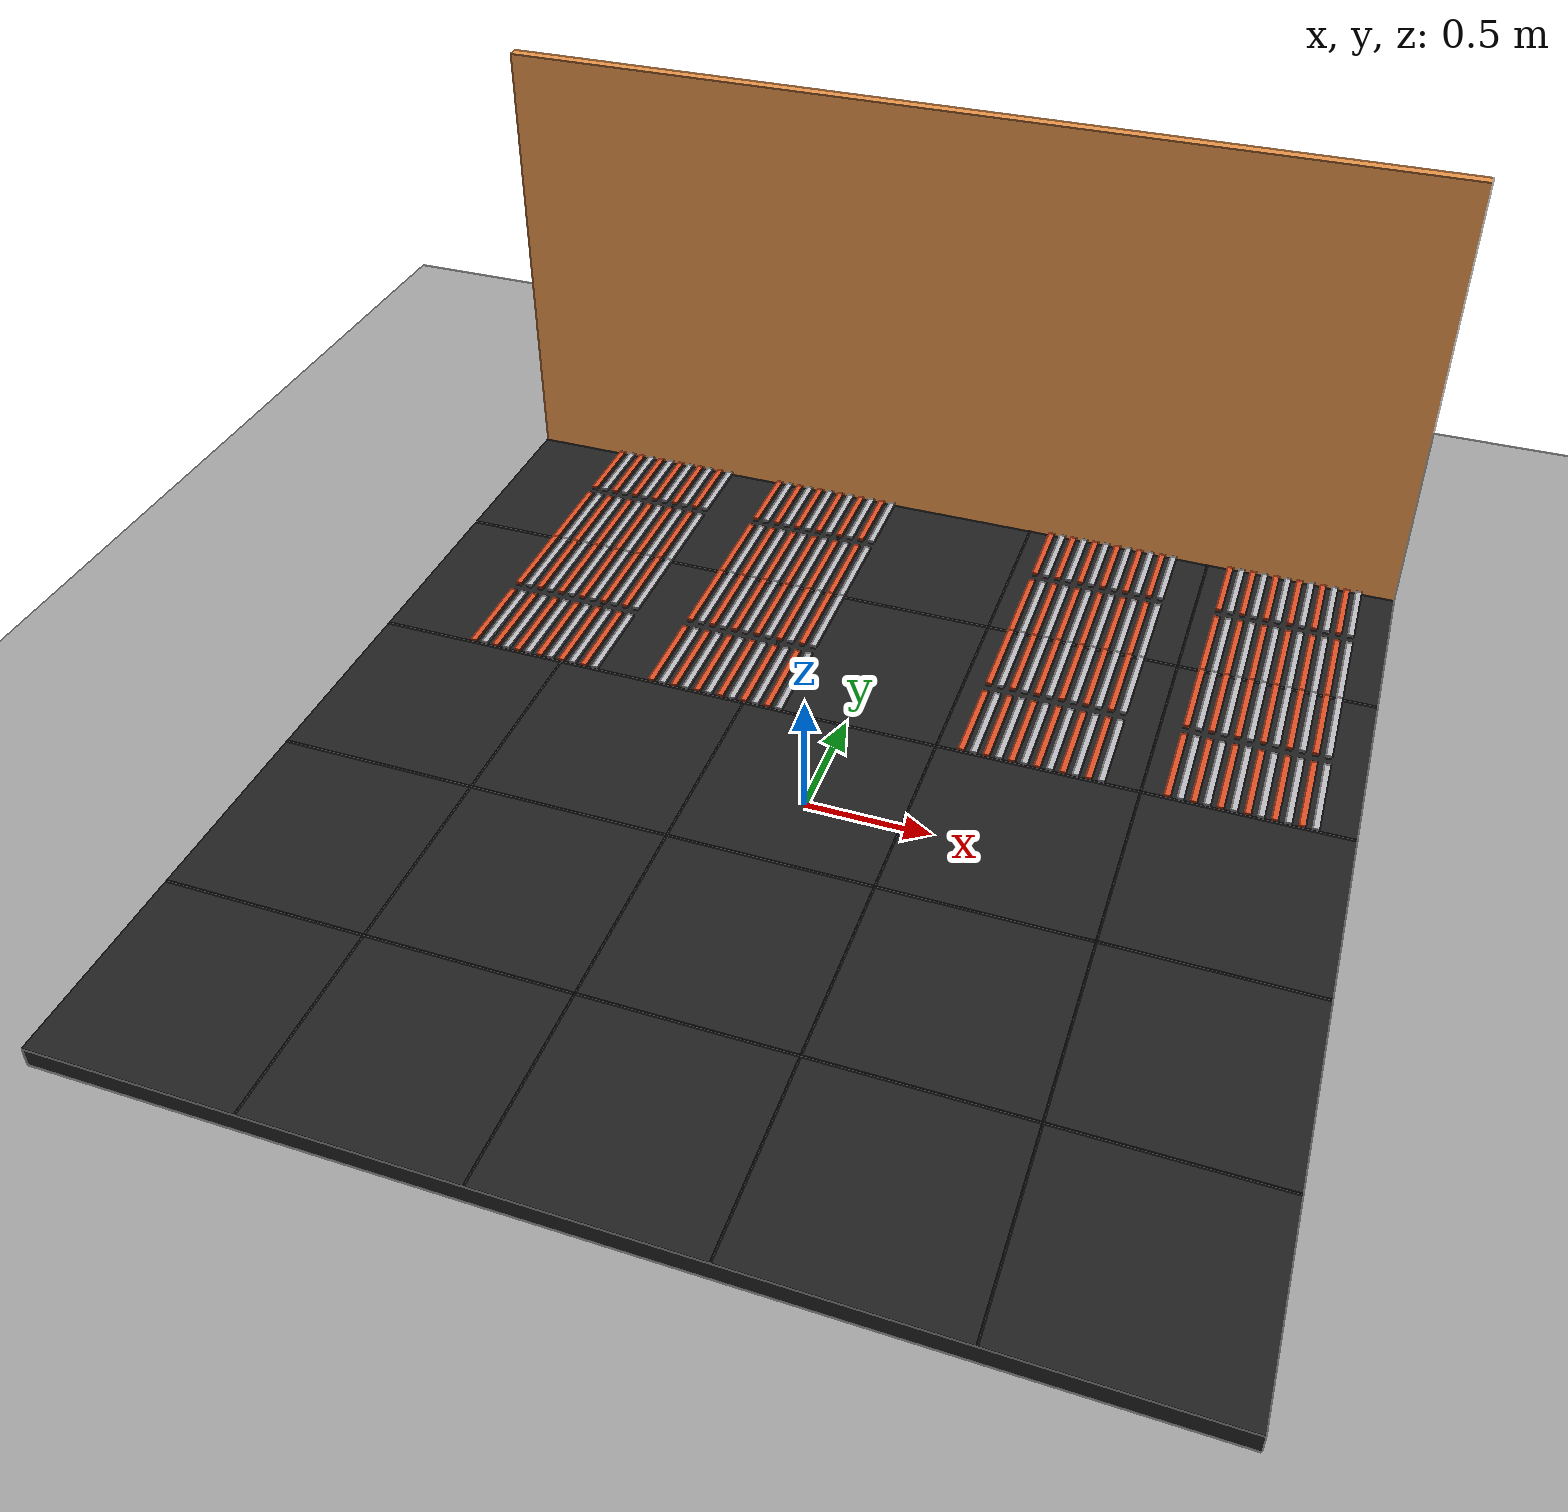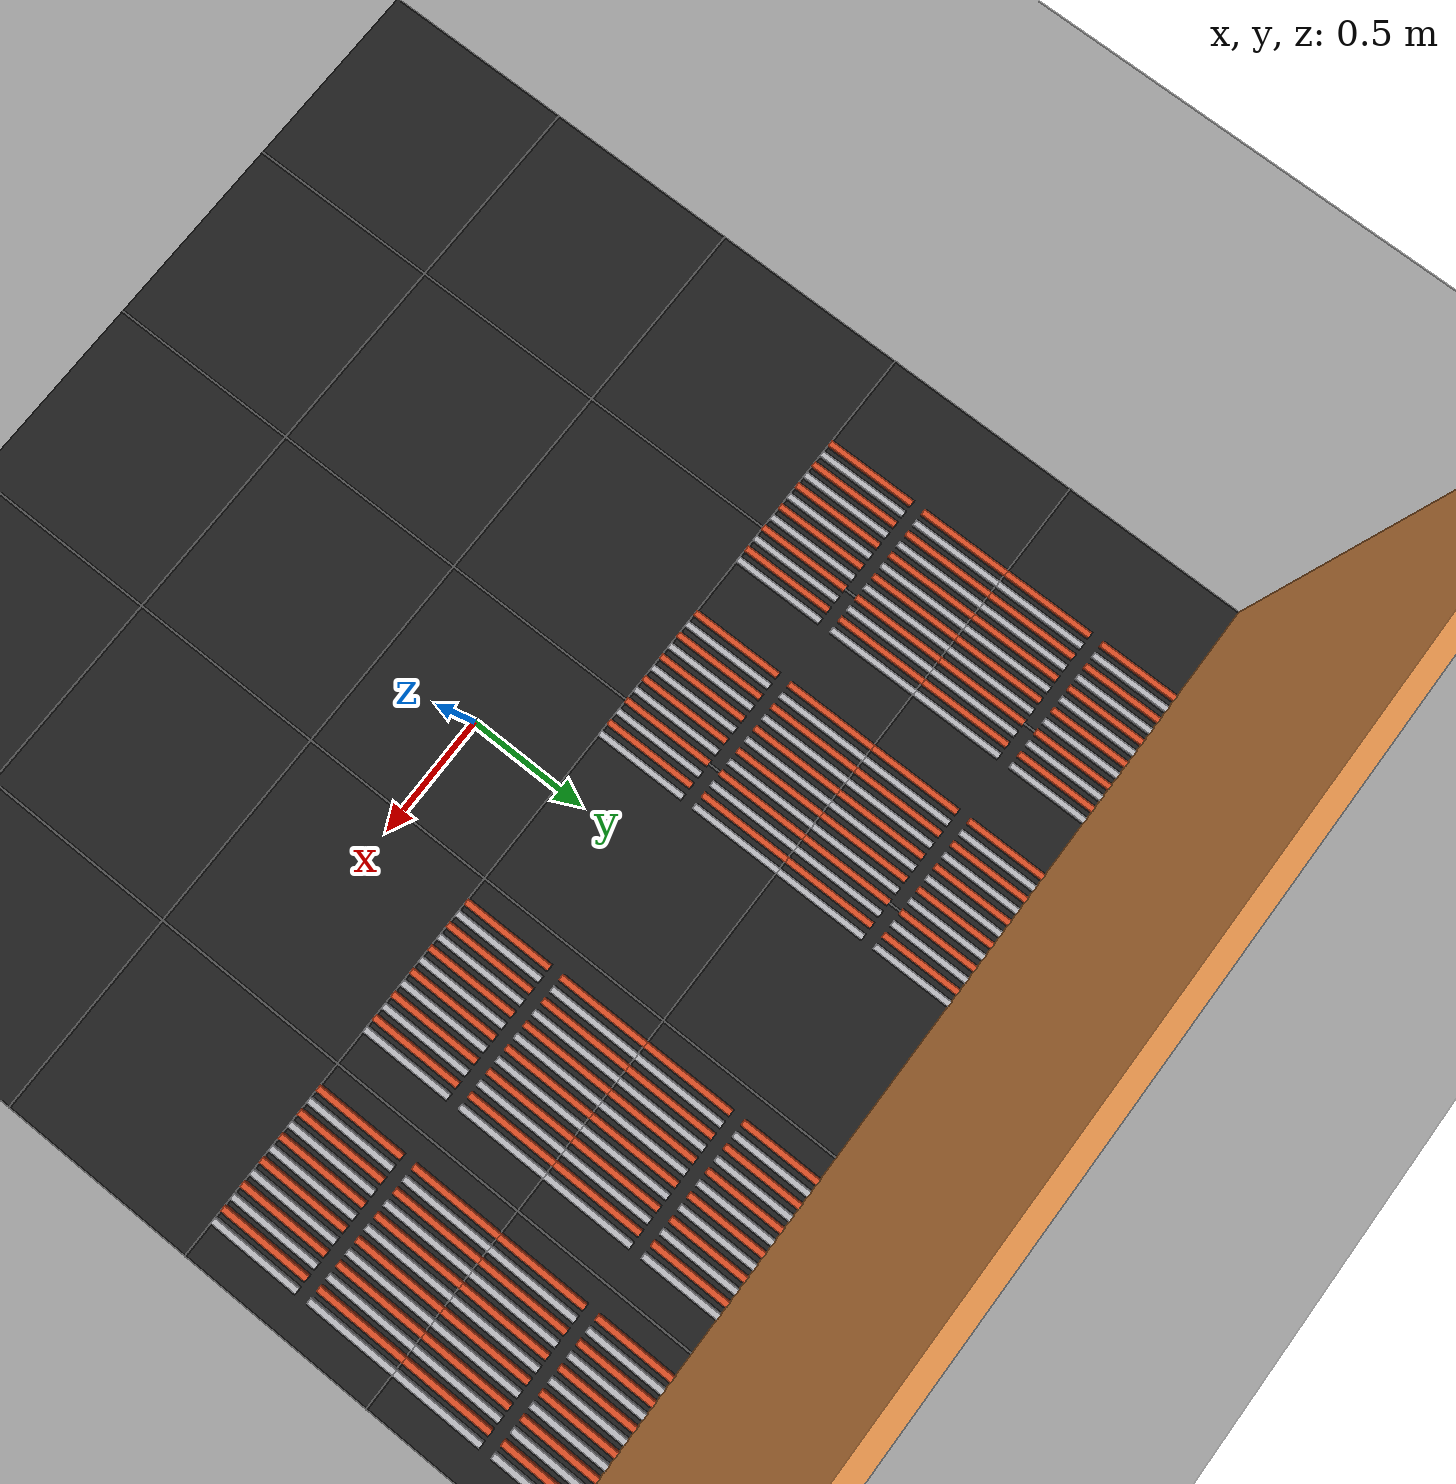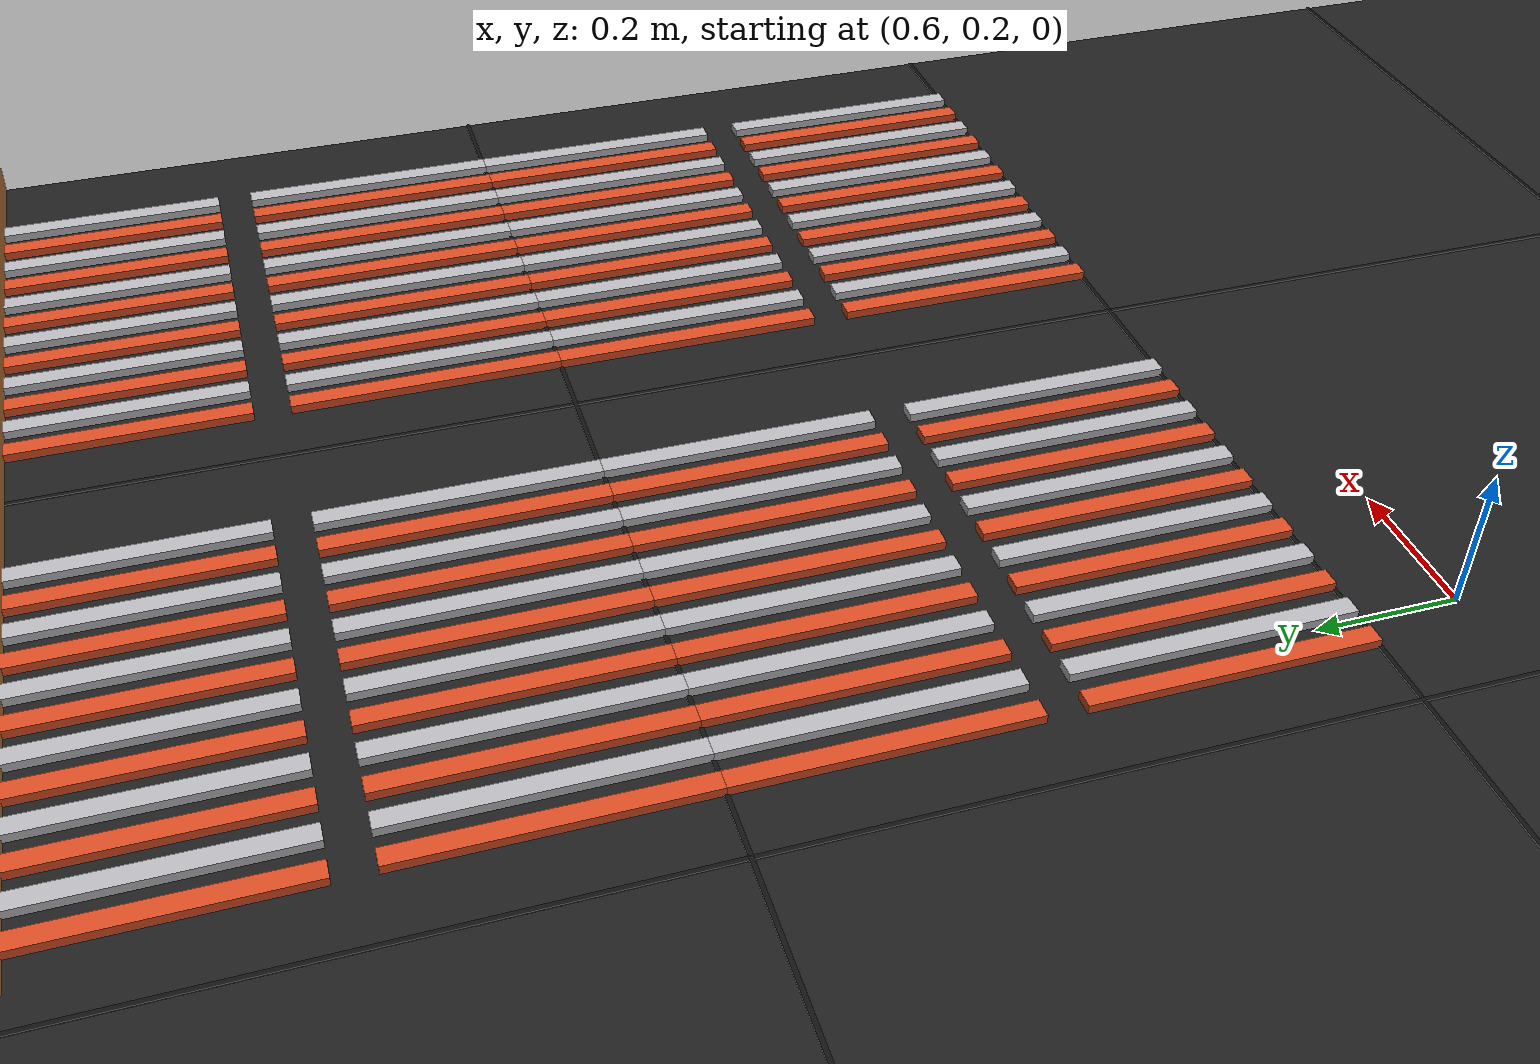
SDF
<?xml version="1.0"?>
<sdf version="1.9">
  <world name="electrolysis_correct_layout">

    <physics name="default_physics" type="ode">
      <max_step_size>0.001</max_step_size>
      <real_time_factor>1.0</real_time_factor>
    </physics>

    <gravity>0 0 -9.81</gravity>

    <scene>
      <ambient>0.55 0.55 0.55 1</ambient>
      <background>0.92 0.92 0.92 1</background>
      <shadows>true</shadows>
    </scene>

    <light name="sun" type="directional">
      <pose>0 0 8 0 0 0</pose>
      <cast_shadows>true</cast_shadows>
      <diffuse>0.95 0.95 0.95 1</diffuse>
      <specular>0.15 0.15 0.15 1</specular>
      <direction>-0.4 0.2 -1</direction>
    </light>

    <model name="ground_plane">
      <static>true</static>
      <link name="link">
        <collision name="collision">
          <geometry>
            <plane><normal>0 0 1</normal><size>20 20</size></plane>
          </geometry>
        </collision>
        <visual name="visual">
          <geometry>
            <plane><normal>0 0 1</normal><size>20 20</size></plane>
          </geometry>
          <material>
            <ambient>0.62 0.62 0.62 1</ambient>
            <diffuse>0.62 0.62 0.62 1</diffuse>
          </material>
        </visual>
      </link>
    </model>

    <model name="polygon_platform">
      <static>true</static>
      <pose>0.0000 0.0000 0.0400 0 0 0</pose>
      <link name="link">
        <collision name="collision">
          <geometry>
            <box><size>4.0000 4.0000 0.0800</size></box>
          </geometry>
        </collision>
        <visual name="visual">
          <geometry>
            <box><size>4.0000 4.0000 0.0800</size></box>
          </geometry>
          <material>
            <ambient>0.12 0.12 0.12 1</ambient>
            <diffuse>0.12 0.12 0.12 1</diffuse>
          </material>
        </visual>
      </link>
    </model>

    <model name="grid_vertical_1">
      <static>true</static>
      <pose>-1.2000 0.0000 0.0810 0 0 0</pose>
      <link name="link">
        <collision name="collision">
          <geometry>
            <box><size>0.0060 4.0000 0.0020</size></box>
          </geometry>
        </collision>
        <visual name="visual">
          <geometry>
            <box><size>0.0060 4.0000 0.0020</size></box>
          </geometry>
          <material>
            <ambient>0.07 0.07 0.07 1</ambient>
            <diffuse>0.07 0.07 0.07 1</diffuse>
          </material>
        </visual>
      </link>
    </model>

    <model name="grid_horizontal_1">
      <static>true</static>
      <pose>0.0000 -1.2000 0.0810 0 0 0</pose>
      <link name="link">
        <collision name="collision">
          <geometry>
            <box><size>4.0000 0.0060 0.0020</size></box>
          </geometry>
        </collision>
        <visual name="visual">
          <geometry>
            <box><size>4.0000 0.0060 0.0020</size></box>
          </geometry>
          <material>
            <ambient>0.07 0.07 0.07 1</ambient>
            <diffuse>0.07 0.07 0.07 1</diffuse>
          </material>
        </visual>
      </link>
    </model>

    <model name="grid_vertical_2">
      <static>true</static>
      <pose>-0.4000 0.0000 0.0810 0 0 0</pose>
      <link name="link">
        <collision name="collision">
          <geometry>
            <box><size>0.0060 4.0000 0.0020</size></box>
          </geometry>
        </collision>
        <visual name="visual">
          <geometry>
            <box><size>0.0060 4.0000 0.0020</size></box>
          </geometry>
          <material>
            <ambient>0.07 0.07 0.07 1</ambient>
            <diffuse>0.07 0.07 0.07 1</diffuse>
          </material>
        </visual>
      </link>
    </model>

    <model name="grid_horizontal_2">
      <static>true</static>
      <pose>0.0000 -0.4000 0.0810 0 0 0</pose>
      <link name="link">
        <collision name="collision">
          <geometry>
            <box><size>4.0000 0.0060 0.0020</size></box>
          </geometry>
        </collision>
        <visual name="visual">
          <geometry>
            <box><size>4.0000 0.0060 0.0020</size></box>
          </geometry>
          <material>
            <ambient>0.07 0.07 0.07 1</ambient>
            <diffuse>0.07 0.07 0.07 1</diffuse>
          </material>
        </visual>
      </link>
    </model>

    <model name="grid_vertical_3">
      <static>true</static>
      <pose>0.4000 0.0000 0.0810 0 0 0</pose>
      <link name="link">
        <collision name="collision">
          <geometry>
            <box><size>0.0060 4.0000 0.0020</size></box>
          </geometry>
        </collision>
        <visual name="visual">
          <geometry>
            <box><size>0.0060 4.0000 0.0020</size></box>
          </geometry>
          <material>
            <ambient>0.07 0.07 0.07 1</ambient>
            <diffuse>0.07 0.07 0.07 1</diffuse>
          </material>
        </visual>
      </link>
    </model>

    <model name="grid_horizontal_3">
      <static>true</static>
      <pose>0.0000 0.4000 0.0810 0 0 0</pose>
      <link name="link">
        <collision name="collision">
          <geometry>
            <box><size>4.0000 0.0060 0.0020</size></box>
          </geometry>
        </collision>
        <visual name="visual">
          <geometry>
            <box><size>4.0000 0.0060 0.0020</size></box>
          </geometry>
          <material>
            <ambient>0.07 0.07 0.07 1</ambient>
            <diffuse>0.07 0.07 0.07 1</diffuse>
          </material>
        </visual>
      </link>
    </model>

    <model name="grid_vertical_4">
      <static>true</static>
      <pose>1.2000 0.0000 0.0810 0 0 0</pose>
      <link name="link">
        <collision name="collision">
          <geometry>
            <box><size>0.0060 4.0000 0.0020</size></box>
          </geometry>
        </collision>
        <visual name="visual">
          <geometry>
            <box><size>0.0060 4.0000 0.0020</size></box>
          </geometry>
          <material>
            <ambient>0.07 0.07 0.07 1</ambient>
            <diffuse>0.07 0.07 0.07 1</diffuse>
          </material>
        </visual>
      </link>
    </model>

    <model name="grid_horizontal_4">
      <static>true</static>
      <pose>0.0000 1.2000 0.0810 0 0 0</pose>
      <link name="link">
        <collision name="collision">
          <geometry>
            <box><size>4.0000 0.0060 0.0020</size></box>
          </geometry>
        </collision>
        <visual name="visual">
          <geometry>
            <box><size>4.0000 0.0060 0.0020</size></box>
          </geometry>
          <material>
            <ambient>0.07 0.07 0.07 1</ambient>
            <diffuse>0.07 0.07 0.07 1</diffuse>
          </material>
        </visual>
      </link>
    </model>

    <model name="left_bath_01_anode_01">
      <static>true</static>
      <pose>-1.6000 0.5875 0.0800 0 0 0</pose>
      <link name="link">
        <collision name="collision">
          <geometry>
            <box><size>0.0250 0.3750 0.0250</size></box>
          </geometry>
        </collision>
        <visual name="visual">
          <geometry>
            <box><size>0.0250 0.3750 0.0250</size></box>
          </geometry>
          <material>
            <ambient>0.85 0.30 0.14 1</ambient>
            <diffuse>0.85 0.30 0.14 1</diffuse>
          </material>
        </visual>
      </link>
    </model>

    <model name="left_bath_01_cathode_02">
      <static>true</static>
      <pose>-1.5500 0.5875 0.0800 0 0 0</pose>
      <link name="link">
        <collision name="collision">
          <geometry>
            <box><size>0.0250 0.3750 0.0250</size></box>
          </geometry>
        </collision>
        <visual name="visual">
          <geometry>
            <box><size>0.0250 0.3750 0.0250</size></box>
          </geometry>
          <material>
            <ambient>0.72 0.72 0.74 1</ambient>
            <diffuse>0.72 0.72 0.74 1</diffuse>
          </material>
        </visual>
      </link>
    </model>

    <model name="left_bath_01_anode_03">
      <static>true</static>
      <pose>-1.5000 0.5875 0.0800 0 0 0</pose>
      <link name="link">
        <collision name="collision">
          <geometry>
            <box><size>0.0250 0.3750 0.0250</size></box>
          </geometry>
        </collision>
        <visual name="visual">
          <geometry>
            <box><size>0.0250 0.3750 0.0250</size></box>
          </geometry>
          <material>
            <ambient>0.85 0.30 0.14 1</ambient>
            <diffuse>0.85 0.30 0.14 1</diffuse>
          </material>
        </visual>
      </link>
    </model>

    <model name="left_bath_01_cathode_04">
      <static>true</static>
      <pose>-1.4500 0.5875 0.0800 0 0 0</pose>
      <link name="link">
        <collision name="collision">
          <geometry>
            <box><size>0.0250 0.3750 0.0250</size></box>
          </geometry>
        </collision>
        <visual name="visual">
          <geometry>
            <box><size>0.0250 0.3750 0.0250</size></box>
          </geometry>
          <material>
            <ambient>0.72 0.72 0.74 1</ambient>
            <diffuse>0.72 0.72 0.74 1</diffuse>
          </material>
        </visual>
      </link>
    </model>

    <model name="left_bath_01_anode_05">
      <static>true</static>
      <pose>-1.4000 0.5875 0.0800 0 0 0</pose>
      <link name="link">
        <collision name="collision">
          <geometry>
            <box><size>0.0250 0.3750 0.0250</size></box>
          </geometry>
        </collision>
        <visual name="visual">
          <geometry>
            <box><size>0.0250 0.3750 0.0250</size></box>
          </geometry>
          <material>
            <ambient>0.85 0.30 0.14 1</ambient>
            <diffuse>0.85 0.30 0.14 1</diffuse>
          </material>
        </visual>
      </link>
    </model>

    <model name="left_bath_01_cathode_06">
      <static>true</static>
      <pose>-1.3500 0.5875 0.0800 0 0 0</pose>
      <link name="link">
        <collision name="collision">
          <geometry>
            <box><size>0.0250 0.3750 0.0250</size></box>
          </geometry>
        </collision>
        <visual name="visual">
          <geometry>
            <box><size>0.0250 0.3750 0.0250</size></box>
          </geometry>
          <material>
            <ambient>0.72 0.72 0.74 1</ambient>
            <diffuse>0.72 0.72 0.74 1</diffuse>
          </material>
        </visual>
      </link>
    </model>

    <model name="left_bath_01_anode_07">
      <static>true</static>
      <pose>-1.3000 0.5875 0.0800 0 0 0</pose>
      <link name="link">
        <collision name="collision">
          <geometry>
            <box><size>0.0250 0.3750 0.0250</size></box>
          </geometry>
        </collision>
        <visual name="visual">
          <geometry>
            <box><size>0.0250 0.3750 0.0250</size></box>
          </geometry>
          <material>
            <ambient>0.85 0.30 0.14 1</ambient>
            <diffuse>0.85 0.30 0.14 1</diffuse>
          </material>
        </visual>
      </link>
    </model>

    <model name="left_bath_01_cathode_08">
      <static>true</static>
      <pose>-1.2500 0.5875 0.0800 0 0 0</pose>
      <link name="link">
        <collision name="collision">
          <geometry>
            <box><size>0.0250 0.3750 0.0250</size></box>
          </geometry>
        </collision>
        <visual name="visual">
          <geometry>
            <box><size>0.0250 0.3750 0.0250</size></box>
          </geometry>
          <material>
            <ambient>0.72 0.72 0.74 1</ambient>
            <diffuse>0.72 0.72 0.74 1</diffuse>
          </material>
        </visual>
      </link>
    </model>

    <model name="left_bath_01_anode_09">
      <static>true</static>
      <pose>-1.2000 0.5875 0.0800 0 0 0</pose>
      <link name="link">
        <collision name="collision">
          <geometry>
            <box><size>0.0250 0.3750 0.0250</size></box>
          </geometry>
        </collision>
        <visual name="visual">
          <geometry>
            <box><size>0.0250 0.3750 0.0250</size></box>
          </geometry>
          <material>
            <ambient>0.85 0.30 0.14 1</ambient>
            <diffuse>0.85 0.30 0.14 1</diffuse>
          </material>
        </visual>
      </link>
    </model>

    <model name="left_bath_01_cathode_10">
      <static>true</static>
      <pose>-1.1500 0.5875 0.0800 0 0 0</pose>
      <link name="link">
        <collision name="collision">
          <geometry>
            <box><size>0.0250 0.3750 0.0250</size></box>
          </geometry>
        </collision>
        <visual name="visual">
          <geometry>
            <box><size>0.0250 0.3750 0.0250</size></box>
          </geometry>
          <material>
            <ambient>0.72 0.72 0.74 1</ambient>
            <diffuse>0.72 0.72 0.74 1</diffuse>
          </material>
        </visual>
      </link>
    </model>

    <model name="left_bath_01_anode_11">
      <static>true</static>
      <pose>-1.1000 0.5875 0.0800 0 0 0</pose>
      <link name="link">
        <collision name="collision">
          <geometry>
            <box><size>0.0250 0.3750 0.0250</size></box>
          </geometry>
        </collision>
        <visual name="visual">
          <geometry>
            <box><size>0.0250 0.3750 0.0250</size></box>
          </geometry>
          <material>
            <ambient>0.85 0.30 0.14 1</ambient>
            <diffuse>0.85 0.30 0.14 1</diffuse>
          </material>
        </visual>
      </link>
    </model>

    <model name="left_bath_01_cathode_12">
      <static>true</static>
      <pose>-1.0500 0.5875 0.0800 0 0 0</pose>
      <link name="link">
        <collision name="collision">
          <geometry>
            <box><size>0.0250 0.3750 0.0250</size></box>
          </geometry>
        </collision>
        <visual name="visual">
          <geometry>
            <box><size>0.0250 0.3750 0.0250</size></box>
          </geometry>
          <material>
            <ambient>0.72 0.72 0.74 1</ambient>
            <diffuse>0.72 0.72 0.74 1</diffuse>
          </material>
        </visual>
      </link>
    </model>

    <model name="left_bath_02_anode_01">
      <static>true</static>
      <pose>-1.6000 1.0125 0.0800 0 0 0</pose>
      <link name="link">
        <collision name="collision">
          <geometry>
            <box><size>0.0250 0.3750 0.0250</size></box>
          </geometry>
        </collision>
        <visual name="visual">
          <geometry>
            <box><size>0.0250 0.3750 0.0250</size></box>
          </geometry>
          <material>
            <ambient>0.85 0.30 0.14 1</ambient>
            <diffuse>0.85 0.30 0.14 1</diffuse>
          </material>
        </visual>
      </link>
    </model>

    <model name="left_bath_02_cathode_02">
      <static>true</static>
      <pose>-1.5500 1.0125 0.0800 0 0 0</pose>
      <link name="link">
        <collision name="collision">
          <geometry>
            <box><size>0.0250 0.3750 0.0250</size></box>
          </geometry>
        </collision>
        <visual name="visual">
          <geometry>
            <box><size>0.0250 0.3750 0.0250</size></box>
          </geometry>
          <material>
            <ambient>0.72 0.72 0.74 1</ambient>
            <diffuse>0.72 0.72 0.74 1</diffuse>
          </material>
        </visual>
      </link>
    </model>

    <model name="left_bath_02_anode_03">
      <static>true</static>
      <pose>-1.5000 1.0125 0.0800 0 0 0</pose>
      <link name="link">
        <collision name="collision">
          <geometry>
            <box><size>0.0250 0.3750 0.0250</size></box>
          </geometry>
        </collision>
        <visual name="visual">
          <geometry>
            <box><size>0.0250 0.3750 0.0250</size></box>
          </geometry>
          <material>
            <ambient>0.85 0.30 0.14 1</ambient>
            <diffuse>0.85 0.30 0.14 1</diffuse>
          </material>
        </visual>
      </link>
    </model>

    <model name="left_bath_02_cathode_04">
      <static>true</static>
      <pose>-1.4500 1.0125 0.0800 0 0 0</pose>
      <link name="link">
        <collision name="collision">
          <geometry>
            <box><size>0.0250 0.3750 0.0250</size></box>
          </geometry>
        </collision>
        <visual name="visual">
          <geometry>
            <box><size>0.0250 0.3750 0.0250</size></box>
          </geometry>
          <material>
            <ambient>0.72 0.72 0.74 1</ambient>
            <diffuse>0.72 0.72 0.74 1</diffuse>
          </material>
        </visual>
      </link>
    </model>

    <model name="left_bath_02_anode_05">
      <static>true</static>
      <pose>-1.4000 1.0125 0.0800 0 0 0</pose>
      <link name="link">
        <collision name="collision">
          <geometry>
            <box><size>0.0250 0.3750 0.0250</size></box>
          </geometry>
        </collision>
        <visual name="visual">
          <geometry>
            <box><size>0.0250 0.3750 0.0250</size></box>
          </geometry>
          <material>
            <ambient>0.85 0.30 0.14 1</ambient>
            <diffuse>0.85 0.30 0.14 1</diffuse>
          </material>
        </visual>
      </link>
    </model>

    <model name="left_bath_02_cathode_06">
      <static>true</static>
      <pose>-1.3500 1.0125 0.0800 0 0 0</pose>
      <link name="link">
        <collision name="collision">
          <geometry>
            <box><size>0.0250 0.3750 0.0250</size></box>
          </geometry>
        </collision>
        <visual name="visual">
          <geometry>
            <box><size>0.0250 0.3750 0.0250</size></box>
          </geometry>
          <material>
            <ambient>0.72 0.72 0.74 1</ambient>
            <diffuse>0.72 0.72 0.74 1</diffuse>
          </material>
        </visual>
      </link>
    </model>

    <model name="left_bath_02_anode_07">
      <static>true</static>
      <pose>-1.3000 1.0125 0.0800 0 0 0</pose>
      <link name="link">
        <collision name="collision">
          <geometry>
            <box><size>0.0250 0.3750 0.0250</size></box>
          </geometry>
        </collision>
        <visual name="visual">
          <geometry>
            <box><size>0.0250 0.3750 0.0250</size></box>
          </geometry>
          <material>
            <ambient>0.85 0.30 0.14 1</ambient>
            <diffuse>0.85 0.30 0.14 1</diffuse>
          </material>
        </visual>
      </link>
    </model>

    <model name="left_bath_02_cathode_08">
      <static>true</static>
      <pose>-1.2500 1.0125 0.0800 0 0 0</pose>
      <link name="link">
        <collision name="collision">
          <geometry>
            <box><size>0.0250 0.3750 0.0250</size></box>
          </geometry>
        </collision>
        <visual name="visual">
          <geometry>
            <box><size>0.0250 0.3750 0.0250</size></box>
          </geometry>
          <material>
            <ambient>0.72 0.72 0.74 1</ambient>
            <diffuse>0.72 0.72 0.74 1</diffuse>
          </material>
        </visual>
      </link>
    </model>

    <model name="left_bath_02_anode_09">
      <static>true</static>
      <pose>-1.2000 1.0125 0.0800 0 0 0</pose>
      <link name="link">
        <collision name="collision">
          <geometry>
            <box><size>0.0250 0.3750 0.0250</size></box>
          </geometry>
        </collision>
        <visual name="visual">
          <geometry>
            <box><size>0.0250 0.3750 0.0250</size></box>
          </geometry>
          <material>
            <ambient>0.85 0.30 0.14 1</ambient>
            <diffuse>0.85 0.30 0.14 1</diffuse>
          </material>
        </visual>
      </link>
    </model>

    <model name="left_bath_02_cathode_10">
      <static>true</static>
      <pose>-1.1500 1.0125 0.0800 0 0 0</pose>
      <link name="link">
        <collision name="collision">
          <geometry>
            <box><size>0.0250 0.3750 0.0250</size></box>
          </geometry>
        </collision>
        <visual name="visual">
          <geometry>
            <box><size>0.0250 0.3750 0.0250</size></box>
          </geometry>
          <material>
            <ambient>0.72 0.72 0.74 1</ambient>
            <diffuse>0.72 0.72 0.74 1</diffuse>
          </material>
        </visual>
      </link>
    </model>

    <model name="left_bath_02_anode_11">
      <static>true</static>
      <pose>-1.1000 1.0125 0.0800 0 0 0</pose>
      <link name="link">
        <collision name="collision">
          <geometry>
            <box><size>0.0250 0.3750 0.0250</size></box>
          </geometry>
        </collision>
        <visual name="visual">
          <geometry>
            <box><size>0.0250 0.3750 0.0250</size></box>
          </geometry>
          <material>
            <ambient>0.85 0.30 0.14 1</ambient>
            <diffuse>0.85 0.30 0.14 1</diffuse>
          </material>
        </visual>
      </link>
    </model>

    <model name="left_bath_02_cathode_12">
      <static>true</static>
      <pose>-1.0500 1.0125 0.0800 0 0 0</pose>
      <link name="link">
        <collision name="collision">
          <geometry>
            <box><size>0.0250 0.3750 0.0250</size></box>
          </geometry>
        </collision>
        <visual name="visual">
          <geometry>
            <box><size>0.0250 0.3750 0.0250</size></box>
          </geometry>
          <material>
            <ambient>0.72 0.72 0.74 1</ambient>
            <diffuse>0.72 0.72 0.74 1</diffuse>
          </material>
        </visual>
      </link>
    </model>

    <model name="left_bath_03_anode_01">
      <static>true</static>
      <pose>-0.8000 0.5875 0.0800 0 0 0</pose>
      <link name="link">
        <collision name="collision">
          <geometry>
            <box><size>0.0250 0.3750 0.0250</size></box>
          </geometry>
        </collision>
        <visual name="visual">
          <geometry>
            <box><size>0.0250 0.3750 0.0250</size></box>
          </geometry>
          <material>
            <ambient>0.85 0.30 0.14 1</ambient>
            <diffuse>0.85 0.30 0.14 1</diffuse>
          </material>
        </visual>
      </link>
    </model>

    <model name="left_bath_03_cathode_02">
      <static>true</static>
      <pose>-0.7500 0.5875 0.0800 0 0 0</pose>
      <link name="link">
        <collision name="collision">
          <geometry>
            <box><size>0.0250 0.3750 0.0250</size></box>
          </geometry>
        </collision>
        <visual name="visual">
          <geometry>
            <box><size>0.0250 0.3750 0.0250</size></box>
          </geometry>
          <material>
            <ambient>0.72 0.72 0.74 1</ambient>
            <diffuse>0.72 0.72 0.74 1</diffuse>
          </material>
        </visual>
      </link>
    </model>

    <model name="left_bath_03_anode_03">
      <static>true</static>
      <pose>-0.7000 0.5875 0.0800 0 0 0</pose>
      <link name="link">
        <collision name="collision">
          <geometry>
            <box><size>0.0250 0.3750 0.0250</size></box>
          </geometry>
        </collision>
        <visual name="visual">
          <geometry>
            <box><size>0.0250 0.3750 0.0250</size></box>
          </geometry>
          <material>
            <ambient>0.85 0.30 0.14 1</ambient>
            <diffuse>0.85 0.30 0.14 1</diffuse>
          </material>
        </visual>
      </link>
    </model>

    <model name="left_bath_03_cathode_04">
      <static>true</static>
      <pose>-0.6500 0.5875 0.0800 0 0 0</pose>
      <link name="link">
        <collision name="collision">
          <geometry>
            <box><size>0.0250 0.3750 0.0250</size></box>
          </geometry>
        </collision>
        <visual name="visual">
          <geometry>
            <box><size>0.0250 0.3750 0.0250</size></box>
          </geometry>
          <material>
            <ambient>0.72 0.72 0.74 1</ambient>
            <diffuse>0.72 0.72 0.74 1</diffuse>
          </material>
        </visual>
      </link>
    </model>

    <model name="left_bath_03_anode_05">
      <static>true</static>
      <pose>-0.6000 0.5875 0.0800 0 0 0</pose>
      <link name="link">
        <collision name="collision">
          <geometry>
            <box><size>0.0250 0.3750 0.0250</size></box>
          </geometry>
        </collision>
        <visual name="visual">
          <geometry>
            <box><size>0.0250 0.3750 0.0250</size></box>
          </geometry>
          <material>
            <ambient>0.85 0.30 0.14 1</ambient>
            <diffuse>0.85 0.30 0.14 1</diffuse>
          </material>
        </visual>
      </link>
    </model>

    <model name="left_bath_03_cathode_06">
      <static>true</static>
      <pose>-0.5500 0.5875 0.0800 0 0 0</pose>
      <link name="link">
        <collision name="collision">
          <geometry>
            <box><size>0.0250 0.3750 0.0250</size></box>
          </geometry>
        </collision>
        <visual name="visual">
          <geometry>
            <box><size>0.0250 0.3750 0.0250</size></box>
          </geometry>
          <material>
            <ambient>0.72 0.72 0.74 1</ambient>
            <diffuse>0.72 0.72 0.74 1</diffuse>
          </material>
        </visual>
      </link>
    </model>

    <model name="left_bath_03_anode_07">
      <static>true</static>
      <pose>-0.5000 0.5875 0.0800 0 0 0</pose>
      <link name="link">
        <collision name="collision">
          <geometry>
            <box><size>0.0250 0.3750 0.0250</size></box>
          </geometry>
        </collision>
        <visual name="visual">
          <geometry>
            <box><size>0.0250 0.3750 0.0250</size></box>
          </geometry>
          <material>
            <ambient>0.85 0.30 0.14 1</ambient>
            <diffuse>0.85 0.30 0.14 1</diffuse>
          </material>
        </visual>
      </link>
    </model>

    <model name="left_bath_03_cathode_08">
      <static>true</static>
      <pose>-0.4500 0.5875 0.0800 0 0 0</pose>
      <link name="link">
        <collision name="collision">
          <geometry>
            <box><size>0.0250 0.3750 0.0250</size></box>
          </geometry>
        </collision>
        <visual name="visual">
          <geometry>
            <box><size>0.0250 0.3750 0.0250</size></box>
          </geometry>
          <material>
            <ambient>0.72 0.72 0.74 1</ambient>
            <diffuse>0.72 0.72 0.74 1</diffuse>
          </material>
        </visual>
      </link>
    </model>

    <model name="left_bath_03_anode_09">
      <static>true</static>
      <pose>-0.4000 0.5875 0.0800 0 0 0</pose>
      <link name="link">
        <collision name="collision">
          <geometry>
            <box><size>0.0250 0.3750 0.0250</size></box>
          </geometry>
        </collision>
        <visual name="visual">
          <geometry>
            <box><size>0.0250 0.3750 0.0250</size></box>
          </geometry>
          <material>
            <ambient>0.85 0.30 0.14 1</ambient>
            <diffuse>0.85 0.30 0.14 1</diffuse>
          </material>
        </visual>
      </link>
    </model>

    <model name="left_bath_03_cathode_10">
      <static>true</static>
      <pose>-0.3500 0.5875 0.0800 0 0 0</pose>
      <link name="link">
        <collision name="collision">
          <geometry>
            <box><size>0.0250 0.3750 0.0250</size></box>
          </geometry>
        </collision>
        <visual name="visual">
          <geometry>
            <box><size>0.0250 0.3750 0.0250</size></box>
          </geometry>
          <material>
            <ambient>0.72 0.72 0.74 1</ambient>
            <diffuse>0.72 0.72 0.74 1</diffuse>
          </material>
        </visual>
      </link>
    </model>

    <model name="left_bath_03_anode_11">
      <static>true</static>
      <pose>-0.3000 0.5875 0.0800 0 0 0</pose>
      <link name="link">
        <collision name="collision">
          <geometry>
            <box><size>0.0250 0.3750 0.0250</size></box>
          </geometry>
        </collision>
        <visual name="visual">
          <geometry>
            <box><size>0.0250 0.3750 0.0250</size></box>
          </geometry>
          <material>
            <ambient>0.85 0.30 0.14 1</ambient>
            <diffuse>0.85 0.30 0.14 1</diffuse>
          </material>
        </visual>
      </link>
    </model>

    <model name="left_bath_03_cathode_12">
      <static>true</static>
      <pose>-0.2500 0.5875 0.0800 0 0 0</pose>
      <link name="link">
        <collision name="collision">
          <geometry>
            <box><size>0.0250 0.3750 0.0250</size></box>
          </geometry>
        </collision>
        <visual name="visual">
          <geometry>
            <box><size>0.0250 0.3750 0.0250</size></box>
          </geometry>
          <material>
            <ambient>0.72 0.72 0.74 1</ambient>
            <diffuse>0.72 0.72 0.74 1</diffuse>
          </material>
        </visual>
      </link>
    </model>

    <model name="left_bath_04_anode_01">
      <static>true</static>
      <pose>-0.8000 1.0125 0.0800 0 0 0</pose>
      <link name="link">
        <collision name="collision">
          <geometry>
            <box><size>0.0250 0.3750 0.0250</size></box>
          </geometry>
        </collision>
        <visual name="visual">
          <geometry>
            <box><size>0.0250 0.3750 0.0250</size></box>
          </geometry>
          <material>
            <ambient>0.85 0.30 0.14 1</ambient>
            <diffuse>0.85 0.30 0.14 1</diffuse>
          </material>
        </visual>
      </link>
    </model>

    <model name="left_bath_04_cathode_02">
      <static>true</static>
      <pose>-0.7500 1.0125 0.0800 0 0 0</pose>
      <link name="link">
        <collision name="collision">
          <geometry>
            <box><size>0.0250 0.3750 0.0250</size></box>
          </geometry>
        </collision>
        <visual name="visual">
          <geometry>
            <box><size>0.0250 0.3750 0.0250</size></box>
          </geometry>
          <material>
            <ambient>0.72 0.72 0.74 1</ambient>
            <diffuse>0.72 0.72 0.74 1</diffuse>
          </material>
        </visual>
      </link>
    </model>

    <model name="left_bath_04_anode_03">
      <static>true</static>
      <pose>-0.7000 1.0125 0.0800 0 0 0</pose>
      <link name="link">
        <collision name="collision">
          <geometry>
            <box><size>0.0250 0.3750 0.0250</size></box>
          </geometry>
        </collision>
        <visual name="visual">
          <geometry>
            <box><size>0.0250 0.3750 0.0250</size></box>
          </geometry>
          <material>
            <ambient>0.85 0.30 0.14 1</ambient>
            <diffuse>0.85 0.30 0.14 1</diffuse>
          </material>
        </visual>
      </link>
    </model>

    <model name="left_bath_04_cathode_04">
      <static>true</static>
      <pose>-0.6500 1.0125 0.0800 0 0 0</pose>
      <link name="link">
        <collision name="collision">
          <geometry>
            <box><size>0.0250 0.3750 0.0250</size></box>
          </geometry>
        </collision>
        <visual name="visual">
          <geometry>
            <box><size>0.0250 0.3750 0.0250</size></box>
          </geometry>
          <material>
            <ambient>0.72 0.72 0.74 1</ambient>
            <diffuse>0.72 0.72 0.74 1</diffuse>
          </material>
        </visual>
      </link>
    </model>

    <model name="left_bath_04_anode_05">
      <static>true</static>
      <pose>-0.6000 1.0125 0.0800 0 0 0</pose>
      <link name="link">
        <collision name="collision">
          <geometry>
            <box><size>0.0250 0.3750 0.0250</size></box>
          </geometry>
        </collision>
        <visual name="visual">
          <geometry>
            <box><size>0.0250 0.3750 0.0250</size></box>
          </geometry>
          <material>
            <ambient>0.85 0.30 0.14 1</ambient>
            <diffuse>0.85 0.30 0.14 1</diffuse>
          </material>
        </visual>
      </link>
    </model>

    <model name="left_bath_04_cathode_06">
      <static>true</static>
      <pose>-0.5500 1.0125 0.0800 0 0 0</pose>
      <link name="link">
        <collision name="collision">
          <geometry>
            <box><size>0.0250 0.3750 0.0250</size></box>
          </geometry>
        </collision>
        <visual name="visual">
          <geometry>
            <box><size>0.0250 0.3750 0.0250</size></box>
          </geometry>
          <material>
            <ambient>0.72 0.72 0.74 1</ambient>
            <diffuse>0.72 0.72 0.74 1</diffuse>
          </material>
        </visual>
      </link>
    </model>

    <model name="left_bath_04_anode_07">
      <static>true</static>
      <pose>-0.5000 1.0125 0.0800 0 0 0</pose>
      <link name="link">
        <collision name="collision">
          <geometry>
            <box><size>0.0250 0.3750 0.0250</size></box>
          </geometry>
        </collision>
        <visual name="visual">
          <geometry>
            <box><size>0.0250 0.3750 0.0250</size></box>
          </geometry>
          <material>
            <ambient>0.85 0.30 0.14 1</ambient>
            <diffuse>0.85 0.30 0.14 1</diffuse>
          </material>
        </visual>
      </link>
    </model>

    <model name="left_bath_04_cathode_08">
      <static>true</static>
      <pose>-0.4500 1.0125 0.0800 0 0 0</pose>
      <link name="link">
        <collision name="collision">
          <geometry>
            <box><size>0.0250 0.3750 0.0250</size></box>
          </geometry>
        </collision>
        <visual name="visual">
          <geometry>
            <box><size>0.0250 0.3750 0.0250</size></box>
          </geometry>
          <material>
            <ambient>0.72 0.72 0.74 1</ambient>
            <diffuse>0.72 0.72 0.74 1</diffuse>
          </material>
        </visual>
      </link>
    </model>

    <model name="left_bath_04_anode_09">
      <static>true</static>
      <pose>-0.4000 1.0125 0.0800 0 0 0</pose>
      <link name="link">
        <collision name="collision">
          <geometry>
            <box><size>0.0250 0.3750 0.0250</size></box>
          </geometry>
        </collision>
        <visual name="visual">
          <geometry>
            <box><size>0.0250 0.3750 0.0250</size></box>
          </geometry>
          <material>
            <ambient>0.85 0.30 0.14 1</ambient>
            <diffuse>0.85 0.30 0.14 1</diffuse>
          </material>
        </visual>
      </link>
    </model>

    <model name="left_bath_04_cathode_10">
      <static>true</static>
      <pose>-0.3500 1.0125 0.0800 0 0 0</pose>
      <link name="link">
        <collision name="collision">
          <geometry>
            <box><size>0.0250 0.3750 0.0250</size></box>
          </geometry>
        </collision>
        <visual name="visual">
          <geometry>
            <box><size>0.0250 0.3750 0.0250</size></box>
          </geometry>
          <material>
            <ambient>0.72 0.72 0.74 1</ambient>
            <diffuse>0.72 0.72 0.74 1</diffuse>
          </material>
        </visual>
      </link>
    </model>

    <model name="left_bath_04_anode_11">
      <static>true</static>
      <pose>-0.3000 1.0125 0.0800 0 0 0</pose>
      <link name="link">
        <collision name="collision">
          <geometry>
            <box><size>0.0250 0.3750 0.0250</size></box>
          </geometry>
        </collision>
        <visual name="visual">
          <geometry>
            <box><size>0.0250 0.3750 0.0250</size></box>
          </geometry>
          <material>
            <ambient>0.85 0.30 0.14 1</ambient>
            <diffuse>0.85 0.30 0.14 1</diffuse>
          </material>
        </visual>
      </link>
    </model>

    <model name="left_bath_04_cathode_12">
      <static>true</static>
      <pose>-0.2500 1.0125 0.0800 0 0 0</pose>
      <link name="link">
        <collision name="collision">
          <geometry>
            <box><size>0.0250 0.3750 0.0250</size></box>
          </geometry>
        </collision>
        <visual name="visual">
          <geometry>
            <box><size>0.0250 0.3750 0.0250</size></box>
          </geometry>
          <material>
            <ambient>0.72 0.72 0.74 1</ambient>
            <diffuse>0.72 0.72 0.74 1</diffuse>
          </material>
        </visual>
      </link>
    </model>

    <model name="left_bath_05_anode_01">
      <static>true</static>
      <pose>-1.6000 1.3875 0.0800 0 0 0</pose>
      <link name="link">
        <collision name="collision">
          <geometry>
            <box><size>0.0250 0.3750 0.0250</size></box>
          </geometry>
        </collision>
        <visual name="visual">
          <geometry>
            <box><size>0.0250 0.3750 0.0250</size></box>
          </geometry>
          <material>
            <ambient>0.85 0.30 0.14 1</ambient>
            <diffuse>0.85 0.30 0.14 1</diffuse>
          </material>
        </visual>
      </link>
    </model>

    <model name="left_bath_05_cathode_02">
      <static>true</static>
      <pose>-1.5500 1.3875 0.0800 0 0 0</pose>
      <link name="link">
        <collision name="collision">
          <geometry>
            <box><size>0.0250 0.3750 0.0250</size></box>
          </geometry>
        </collision>
        <visual name="visual">
          <geometry>
            <box><size>0.0250 0.3750 0.0250</size></box>
          </geometry>
          <material>
            <ambient>0.72 0.72 0.74 1</ambient>
            <diffuse>0.72 0.72 0.74 1</diffuse>
          </material>
        </visual>
      </link>
    </model>

    <model name="left_bath_05_anode_03">
      <static>true</static>
      <pose>-1.5000 1.3875 0.0800 0 0 0</pose>
      <link name="link">
        <collision name="collision">
          <geometry>
            <box><size>0.0250 0.3750 0.0250</size></box>
          </geometry>
        </collision>
        <visual name="visual">
          <geometry>
            <box><size>0.0250 0.3750 0.0250</size></box>
          </geometry>
          <material>
            <ambient>0.85 0.30 0.14 1</ambient>
            <diffuse>0.85 0.30 0.14 1</diffuse>
          </material>
        </visual>
      </link>
    </model>

    <model name="left_bath_05_cathode_04">
      <static>true</static>
      <pose>-1.4500 1.3875 0.0800 0 0 0</pose>
      <link name="link">
        <collision name="collision">
          <geometry>
            <box><size>0.0250 0.3750 0.0250</size></box>
          </geometry>
        </collision>
        <visual name="visual">
          <geometry>
            <box><size>0.0250 0.3750 0.0250</size></box>
          </geometry>
          <material>
            <ambient>0.72 0.72 0.74 1</ambient>
            <diffuse>0.72 0.72 0.74 1</diffuse>
          </material>
        </visual>
      </link>
    </model>

    <model name="left_bath_05_anode_05">
      <static>true</static>
      <pose>-1.4000 1.3875 0.0800 0 0 0</pose>
      <link name="link">
        <collision name="collision">
          <geometry>
            <box><size>0.0250 0.3750 0.0250</size></box>
          </geometry>
        </collision>
        <visual name="visual">
          <geometry>
            <box><size>0.0250 0.3750 0.0250</size></box>
          </geometry>
          <material>
            <ambient>0.85 0.30 0.14 1</ambient>
            <diffuse>0.85 0.30 0.14 1</diffuse>
          </material>
        </visual>
      </link>
    </model>

    <model name="left_bath_05_cathode_06">
      <static>true</static>
      <pose>-1.3500 1.3875 0.0800 0 0 0</pose>
      <link name="link">
        <collision name="collision">
          <geometry>
            <box><size>0.0250 0.3750 0.0250</size></box>
          </geometry>
        </collision>
        <visual name="visual">
          <geometry>
            <box><size>0.0250 0.3750 0.0250</size></box>
          </geometry>
          <material>
            <ambient>0.72 0.72 0.74 1</ambient>
            <diffuse>0.72 0.72 0.74 1</diffuse>
          </material>
        </visual>
      </link>
    </model>

    <model name="left_bath_05_anode_07">
      <static>true</static>
      <pose>-1.3000 1.3875 0.0800 0 0 0</pose>
      <link name="link">
        <collision name="collision">
          <geometry>
            <box><size>0.0250 0.3750 0.0250</size></box>
          </geometry>
        </collision>
        <visual name="visual">
          <geometry>
            <box><size>0.0250 0.3750 0.0250</size></box>
          </geometry>
          <material>
            <ambient>0.85 0.30 0.14 1</ambient>
            <diffuse>0.85 0.30 0.14 1</diffuse>
          </material>
        </visual>
      </link>
    </model>

    <model name="left_bath_05_cathode_08">
      <static>true</static>
      <pose>-1.2500 1.3875 0.0800 0 0 0</pose>
      <link name="link">
        <collision name="collision">
          <geometry>
            <box><size>0.0250 0.3750 0.0250</size></box>
          </geometry>
        </collision>
        <visual name="visual">
          <geometry>
            <box><size>0.0250 0.3750 0.0250</size></box>
          </geometry>
          <material>
            <ambient>0.72 0.72 0.74 1</ambient>
            <diffuse>0.72 0.72 0.74 1</diffuse>
          </material>
        </visual>
      </link>
    </model>

    <model name="left_bath_05_anode_09">
      <static>true</static>
      <pose>-1.2000 1.3875 0.0800 0 0 0</pose>
      <link name="link">
        <collision name="collision">
          <geometry>
            <box><size>0.0250 0.3750 0.0250</size></box>
          </geometry>
        </collision>
        <visual name="visual">
          <geometry>
            <box><size>0.0250 0.3750 0.0250</size></box>
          </geometry>
          <material>
            <ambient>0.85 0.30 0.14 1</ambient>
            <diffuse>0.85 0.30 0.14 1</diffuse>
          </material>
        </visual>
      </link>
    </model>

    <model name="left_bath_05_cathode_10">
      <static>true</static>
      <pose>-1.1500 1.3875 0.0800 0 0 0</pose>
      <link name="link">
        <collision name="collision">
          <geometry>
            <box><size>0.0250 0.3750 0.0250</size></box>
          </geometry>
        </collision>
        <visual name="visual">
          <geometry>
            <box><size>0.0250 0.3750 0.0250</size></box>
          </geometry>
          <material>
            <ambient>0.72 0.72 0.74 1</ambient>
            <diffuse>0.72 0.72 0.74 1</diffuse>
          </material>
        </visual>
      </link>
    </model>

    <model name="left_bath_05_anode_11">
      <static>true</static>
      <pose>-1.1000 1.3875 0.0800 0 0 0</pose>
      <link name="link">
        <collision name="collision">
          <geometry>
            <box><size>0.0250 0.3750 0.0250</size></box>
          </geometry>
        </collision>
        <visual name="visual">
          <geometry>
            <box><size>0.0250 0.3750 0.0250</size></box>
          </geometry>
          <material>
            <ambient>0.85 0.30 0.14 1</ambient>
            <diffuse>0.85 0.30 0.14 1</diffuse>
          </material>
        </visual>
      </link>
    </model>

    <model name="left_bath_05_cathode_12">
      <static>true</static>
      <pose>-1.0500 1.3875 0.0800 0 0 0</pose>
      <link name="link">
        <collision name="collision">
          <geometry>
            <box><size>0.0250 0.3750 0.0250</size></box>
          </geometry>
        </collision>
        <visual name="visual">
          <geometry>
            <box><size>0.0250 0.3750 0.0250</size></box>
          </geometry>
          <material>
            <ambient>0.72 0.72 0.74 1</ambient>
            <diffuse>0.72 0.72 0.74 1</diffuse>
          </material>
        </visual>
      </link>
    </model>

    <model name="left_bath_06_anode_01">
      <static>true</static>
      <pose>-1.6000 1.8125 0.0800 0 0 0</pose>
      <link name="link">
        <collision name="collision">
          <geometry>
            <box><size>0.0250 0.3750 0.0250</size></box>
          </geometry>
        </collision>
        <visual name="visual">
          <geometry>
            <box><size>0.0250 0.3750 0.0250</size></box>
          </geometry>
          <material>
            <ambient>0.85 0.30 0.14 1</ambient>
            <diffuse>0.85 0.30 0.14 1</diffuse>
          </material>
        </visual>
      </link>
    </model>

    <model name="left_bath_06_cathode_02">
      <static>true</static>
      <pose>-1.5500 1.8125 0.0800 0 0 0</pose>
      <link name="link">
        <collision name="collision">
          <geometry>
            <box><size>0.0250 0.3750 0.0250</size></box>
          </geometry>
        </collision>
        <visual name="visual">
          <geometry>
            <box><size>0.0250 0.3750 0.0250</size></box>
          </geometry>
          <material>
            <ambient>0.72 0.72 0.74 1</ambient>
            <diffuse>0.72 0.72 0.74 1</diffuse>
          </material>
        </visual>
      </link>
    </model>

    <model name="left_bath_06_anode_03">
      <static>true</static>
      <pose>-1.5000 1.8125 0.0800 0 0 0</pose>
      <link name="link">
        <collision name="collision">
          <geometry>
            <box><size>0.0250 0.3750 0.0250</size></box>
          </geometry>
        </collision>
        <visual name="visual">
          <geometry>
            <box><size>0.0250 0.3750 0.0250</size></box>
          </geometry>
          <material>
            <ambient>0.85 0.30 0.14 1</ambient>
            <diffuse>0.85 0.30 0.14 1</diffuse>
          </material>
        </visual>
      </link>
    </model>

    <model name="left_bath_06_cathode_04">
      <static>true</static>
      <pose>-1.4500 1.8125 0.0800 0 0 0</pose>
      <link name="link">
        <collision name="collision">
          <geometry>
            <box><size>0.0250 0.3750 0.0250</size></box>
          </geometry>
        </collision>
        <visual name="visual">
          <geometry>
            <box><size>0.0250 0.3750 0.0250</size></box>
          </geometry>
          <material>
            <ambient>0.72 0.72 0.74 1</ambient>
            <diffuse>0.72 0.72 0.74 1</diffuse>
          </material>
        </visual>
      </link>
    </model>

    <model name="left_bath_06_anode_05">
      <static>true</static>
      <pose>-1.4000 1.8125 0.0800 0 0 0</pose>
      <link name="link">
        <collision name="collision">
          <geometry>
            <box><size>0.0250 0.3750 0.0250</size></box>
          </geometry>
        </collision>
        <visual name="visual">
          <geometry>
            <box><size>0.0250 0.3750 0.0250</size></box>
          </geometry>
          <material>
            <ambient>0.85 0.30 0.14 1</ambient>
            <diffuse>0.85 0.30 0.14 1</diffuse>
          </material>
        </visual>
      </link>
    </model>

    <model name="left_bath_06_cathode_06">
      <static>true</static>
      <pose>-1.3500 1.8125 0.0800 0 0 0</pose>
      <link name="link">
        <collision name="collision">
          <geometry>
            <box><size>0.0250 0.3750 0.0250</size></box>
          </geometry>
        </collision>
        <visual name="visual">
          <geometry>
            <box><size>0.0250 0.3750 0.0250</size></box>
          </geometry>
          <material>
            <ambient>0.72 0.72 0.74 1</ambient>
            <diffuse>0.72 0.72 0.74 1</diffuse>
          </material>
        </visual>
      </link>
    </model>

    <model name="left_bath_06_anode_07">
      <static>true</static>
      <pose>-1.3000 1.8125 0.0800 0 0 0</pose>
      <link name="link">
        <collision name="collision">
          <geometry>
            <box><size>0.0250 0.3750 0.0250</size></box>
          </geometry>
        </collision>
        <visual name="visual">
          <geometry>
            <box><size>0.0250 0.3750 0.0250</size></box>
          </geometry>
          <material>
            <ambient>0.85 0.30 0.14 1</ambient>
            <diffuse>0.85 0.30 0.14 1</diffuse>
          </material>
        </visual>
      </link>
    </model>

    <model name="left_bath_06_cathode_08">
      <static>true</static>
      <pose>-1.2500 1.8125 0.0800 0 0 0</pose>
      <link name="link">
        <collision name="collision">
          <geometry>
            <box><size>0.0250 0.3750 0.0250</size></box>
          </geometry>
        </collision>
        <visual name="visual">
          <geometry>
            <box><size>0.0250 0.3750 0.0250</size></box>
          </geometry>
          <material>
            <ambient>0.72 0.72 0.74 1</ambient>
            <diffuse>0.72 0.72 0.74 1</diffuse>
          </material>
        </visual>
      </link>
    </model>

    <model name="left_bath_06_anode_09">
      <static>true</static>
      <pose>-1.2000 1.8125 0.0800 0 0 0</pose>
      <link name="link">
        <collision name="collision">
          <geometry>
            <box><size>0.0250 0.3750 0.0250</size></box>
          </geometry>
        </collision>
        <visual name="visual">
          <geometry>
            <box><size>0.0250 0.3750 0.0250</size></box>
          </geometry>
          <material>
            <ambient>0.85 0.30 0.14 1</ambient>
            <diffuse>0.85 0.30 0.14 1</diffuse>
          </material>
        </visual>
      </link>
    </model>

    <model name="left_bath_06_cathode_10">
      <static>true</static>
      <pose>-1.1500 1.8125 0.0800 0 0 0</pose>
      <link name="link">
        <collision name="collision">
          <geometry>
            <box><size>0.0250 0.3750 0.0250</size></box>
          </geometry>
        </collision>
        <visual name="visual">
          <geometry>
            <box><size>0.0250 0.3750 0.0250</size></box>
          </geometry>
          <material>
            <ambient>0.72 0.72 0.74 1</ambient>
            <diffuse>0.72 0.72 0.74 1</diffuse>
          </material>
        </visual>
      </link>
    </model>

    <model name="left_bath_06_anode_11">
      <static>true</static>
      <pose>-1.1000 1.8125 0.0800 0 0 0</pose>
      <link name="link">
        <collision name="collision">
          <geometry>
            <box><size>0.0250 0.3750 0.0250</size></box>
          </geometry>
        </collision>
        <visual name="visual">
          <geometry>
            <box><size>0.0250 0.3750 0.0250</size></box>
          </geometry>
          <material>
            <ambient>0.85 0.30 0.14 1</ambient>
            <diffuse>0.85 0.30 0.14 1</diffuse>
          </material>
        </visual>
      </link>
    </model>

    <model name="left_bath_06_cathode_12">
      <static>true</static>
      <pose>-1.0500 1.8125 0.0800 0 0 0</pose>
      <link name="link">
        <collision name="collision">
          <geometry>
            <box><size>0.0250 0.3750 0.0250</size></box>
          </geometry>
        </collision>
        <visual name="visual">
          <geometry>
            <box><size>0.0250 0.3750 0.0250</size></box>
          </geometry>
          <material>
            <ambient>0.72 0.72 0.74 1</ambient>
            <diffuse>0.72 0.72 0.74 1</diffuse>
          </material>
        </visual>
      </link>
    </model>

    <model name="left_bath_07_anode_01">
      <static>true</static>
      <pose>-0.8000 1.3875 0.0800 0 0 0</pose>
      <link name="link">
        <collision name="collision">
          <geometry>
            <box><size>0.0250 0.3750 0.0250</size></box>
          </geometry>
        </collision>
        <visual name="visual">
          <geometry>
            <box><size>0.0250 0.3750 0.0250</size></box>
          </geometry>
          <material>
            <ambient>0.85 0.30 0.14 1</ambient>
            <diffuse>0.85 0.30 0.14 1</diffuse>
          </material>
        </visual>
      </link>
    </model>

    <model name="left_bath_07_cathode_02">
      <static>true</static>
      <pose>-0.7500 1.3875 0.0800 0 0 0</pose>
      <link name="link">
        <collision name="collision">
          <geometry>
            <box><size>0.0250 0.3750 0.0250</size></box>
          </geometry>
        </collision>
        <visual name="visual">
          <geometry>
            <box><size>0.0250 0.3750 0.0250</size></box>
          </geometry>
          <material>
            <ambient>0.72 0.72 0.74 1</ambient>
            <diffuse>0.72 0.72 0.74 1</diffuse>
          </material>
        </visual>
      </link>
    </model>

    <model name="left_bath_07_anode_03">
      <static>true</static>
      <pose>-0.7000 1.3875 0.0800 0 0 0</pose>
      <link name="link">
        <collision name="collision">
          <geometry>
            <box><size>0.0250 0.3750 0.0250</size></box>
          </geometry>
        </collision>
        <visual name="visual">
          <geometry>
            <box><size>0.0250 0.3750 0.0250</size></box>
          </geometry>
          <material>
            <ambient>0.85 0.30 0.14 1</ambient>
            <diffuse>0.85 0.30 0.14 1</diffuse>
          </material>
        </visual>
      </link>
    </model>

    <model name="left_bath_07_cathode_04">
      <static>true</static>
      <pose>-0.6500 1.3875 0.0800 0 0 0</pose>
      <link name="link">
        <collision name="collision">
          <geometry>
            <box><size>0.0250 0.3750 0.0250</size></box>
          </geometry>
        </collision>
        <visual name="visual">
          <geometry>
            <box><size>0.0250 0.3750 0.0250</size></box>
          </geometry>
          <material>
            <ambient>0.72 0.72 0.74 1</ambient>
            <diffuse>0.72 0.72 0.74 1</diffuse>
          </material>
        </visual>
      </link>
    </model>

    <model name="left_bath_07_anode_05">
      <static>true</static>
      <pose>-0.6000 1.3875 0.0800 0 0 0</pose>
      <link name="link">
        <collision name="collision">
          <geometry>
            <box><size>0.0250 0.3750 0.0250</size></box>
          </geometry>
        </collision>
        <visual name="visual">
          <geometry>
            <box><size>0.0250 0.3750 0.0250</size></box>
          </geometry>
          <material>
            <ambient>0.85 0.30 0.14 1</ambient>
            <diffuse>0.85 0.30 0.14 1</diffuse>
          </material>
        </visual>
      </link>
    </model>

    <model name="left_bath_07_cathode_06">
      <static>true</static>
      <pose>-0.5500 1.3875 0.0800 0 0 0</pose>
      <link name="link">
        <collision name="collision">
          <geometry>
            <box><size>0.0250 0.3750 0.0250</size></box>
          </geometry>
        </collision>
        <visual name="visual">
          <geometry>
            <box><size>0.0250 0.3750 0.0250</size></box>
          </geometry>
          <material>
            <ambient>0.72 0.72 0.74 1</ambient>
            <diffuse>0.72 0.72 0.74 1</diffuse>
          </material>
        </visual>
      </link>
    </model>

    <model name="left_bath_07_anode_07">
      <static>true</static>
      <pose>-0.5000 1.3875 0.0800 0 0 0</pose>
      <link name="link">
        <collision name="collision">
          <geometry>
            <box><size>0.0250 0.3750 0.0250</size></box>
          </geometry>
        </collision>
        <visual name="visual">
          <geometry>
            <box><size>0.0250 0.3750 0.0250</size></box>
          </geometry>
          <material>
            <ambient>0.85 0.30 0.14 1</ambient>
            <diffuse>0.85 0.30 0.14 1</diffuse>
          </material>
        </visual>
      </link>
    </model>

    <model name="left_bath_07_cathode_08">
      <static>true</static>
      <pose>-0.4500 1.3875 0.0800 0 0 0</pose>
      <link name="link">
        <collision name="collision">
          <geometry>
            <box><size>0.0250 0.3750 0.0250</size></box>
          </geometry>
        </collision>
        <visual name="visual">
          <geometry>
            <box><size>0.0250 0.3750 0.0250</size></box>
          </geometry>
          <material>
            <ambient>0.72 0.72 0.74 1</ambient>
            <diffuse>0.72 0.72 0.74 1</diffuse>
          </material>
        </visual>
      </link>
    </model>

    <model name="left_bath_07_anode_09">
      <static>true</static>
      <pose>-0.4000 1.3875 0.0800 0 0 0</pose>
      <link name="link">
        <collision name="collision">
          <geometry>
            <box><size>0.0250 0.3750 0.0250</size></box>
          </geometry>
        </collision>
        <visual name="visual">
          <geometry>
            <box><size>0.0250 0.3750 0.0250</size></box>
          </geometry>
          <material>
            <ambient>0.85 0.30 0.14 1</ambient>
            <diffuse>0.85 0.30 0.14 1</diffuse>
          </material>
        </visual>
      </link>
    </model>

    <model name="left_bath_07_cathode_10">
      <static>true</static>
      <pose>-0.3500 1.3875 0.0800 0 0 0</pose>
      <link name="link">
        <collision name="collision">
          <geometry>
            <box><size>0.0250 0.3750 0.0250</size></box>
          </geometry>
        </collision>
        <visual name="visual">
          <geometry>
            <box><size>0.0250 0.3750 0.0250</size></box>
          </geometry>
          <material>
            <ambient>0.72 0.72 0.74 1</ambient>
            <diffuse>0.72 0.72 0.74 1</diffuse>
          </material>
        </visual>
      </link>
    </model>

    <model name="left_bath_07_anode_11">
      <static>true</static>
      <pose>-0.3000 1.3875 0.0800 0 0 0</pose>
      <link name="link">
        <collision name="collision">
          <geometry>
            <box><size>0.0250 0.3750 0.0250</size></box>
          </geometry>
        </collision>
        <visual name="visual">
          <geometry>
            <box><size>0.0250 0.3750 0.0250</size></box>
          </geometry>
          <material>
            <ambient>0.85 0.30 0.14 1</ambient>
            <diffuse>0.85 0.30 0.14 1</diffuse>
          </material>
        </visual>
      </link>
    </model>

    <model name="left_bath_07_cathode_12">
      <static>true</static>
      <pose>-0.2500 1.3875 0.0800 0 0 0</pose>
      <link name="link">
        <collision name="collision">
          <geometry>
            <box><size>0.0250 0.3750 0.0250</size></box>
          </geometry>
        </collision>
        <visual name="visual">
          <geometry>
            <box><size>0.0250 0.3750 0.0250</size></box>
          </geometry>
          <material>
            <ambient>0.72 0.72 0.74 1</ambient>
            <diffuse>0.72 0.72 0.74 1</diffuse>
          </material>
        </visual>
      </link>
    </model>

    <model name="left_bath_08_anode_01">
      <static>true</static>
      <pose>-0.8000 1.8125 0.0800 0 0 0</pose>
      <link name="link">
        <collision name="collision">
          <geometry>
            <box><size>0.0250 0.3750 0.0250</size></box>
          </geometry>
        </collision>
        <visual name="visual">
          <geometry>
            <box><size>0.0250 0.3750 0.0250</size></box>
          </geometry>
          <material>
            <ambient>0.85 0.30 0.14 1</ambient>
            <diffuse>0.85 0.30 0.14 1</diffuse>
          </material>
        </visual>
      </link>
    </model>

    <model name="left_bath_08_cathode_02">
      <static>true</static>
      <pose>-0.7500 1.8125 0.0800 0 0 0</pose>
      <link name="link">
        <collision name="collision">
          <geometry>
            <box><size>0.0250 0.3750 0.0250</size></box>
          </geometry>
        </collision>
        <visual name="visual">
          <geometry>
            <box><size>0.0250 0.3750 0.0250</size></box>
          </geometry>
          <material>
            <ambient>0.72 0.72 0.74 1</ambient>
            <diffuse>0.72 0.72 0.74 1</diffuse>
          </material>
        </visual>
      </link>
    </model>

    <model name="left_bath_08_anode_03">
      <static>true</static>
      <pose>-0.7000 1.8125 0.0800 0 0 0</pose>
      <link name="link">
        <collision name="collision">
          <geometry>
            <box><size>0.0250 0.3750 0.0250</size></box>
          </geometry>
        </collision>
        <visual name="visual">
          <geometry>
            <box><size>0.0250 0.3750 0.0250</size></box>
          </geometry>
          <material>
            <ambient>0.85 0.30 0.14 1</ambient>
            <diffuse>0.85 0.30 0.14 1</diffuse>
          </material>
        </visual>
      </link>
    </model>

    <model name="left_bath_08_cathode_04">
      <static>true</static>
      <pose>-0.6500 1.8125 0.0800 0 0 0</pose>
      <link name="link">
        <collision name="collision">
          <geometry>
            <box><size>0.0250 0.3750 0.0250</size></box>
          </geometry>
        </collision>
        <visual name="visual">
          <geometry>
            <box><size>0.0250 0.3750 0.0250</size></box>
          </geometry>
          <material>
            <ambient>0.72 0.72 0.74 1</ambient>
            <diffuse>0.72 0.72 0.74 1</diffuse>
          </material>
        </visual>
      </link>
    </model>

    <model name="left_bath_08_anode_05">
      <static>true</static>
      <pose>-0.6000 1.8125 0.0800 0 0 0</pose>
      <link name="link">
        <collision name="collision">
          <geometry>
            <box><size>0.0250 0.3750 0.0250</size></box>
          </geometry>
        </collision>
        <visual name="visual">
          <geometry>
            <box><size>0.0250 0.3750 0.0250</size></box>
          </geometry>
          <material>
            <ambient>0.85 0.30 0.14 1</ambient>
            <diffuse>0.85 0.30 0.14 1</diffuse>
          </material>
        </visual>
      </link>
    </model>

    <model name="left_bath_08_cathode_06">
      <static>true</static>
      <pose>-0.5500 1.8125 0.0800 0 0 0</pose>
      <link name="link">
        <collision name="collision">
          <geometry>
            <box><size>0.0250 0.3750 0.0250</size></box>
          </geometry>
        </collision>
        <visual name="visual">
          <geometry>
            <box><size>0.0250 0.3750 0.0250</size></box>
          </geometry>
          <material>
            <ambient>0.72 0.72 0.74 1</ambient>
            <diffuse>0.72 0.72 0.74 1</diffuse>
          </material>
        </visual>
      </link>
    </model>

    <model name="left_bath_08_anode_07">
      <static>true</static>
      <pose>-0.5000 1.8125 0.0800 0 0 0</pose>
      <link name="link">
        <collision name="collision">
          <geometry>
            <box><size>0.0250 0.3750 0.0250</size></box>
          </geometry>
        </collision>
        <visual name="visual">
          <geometry>
            <box><size>0.0250 0.3750 0.0250</size></box>
          </geometry>
          <material>
            <ambient>0.85 0.30 0.14 1</ambient>
            <diffuse>0.85 0.30 0.14 1</diffuse>
          </material>
        </visual>
      </link>
    </model>

    <model name="left_bath_08_cathode_08">
      <static>true</static>
      <pose>-0.4500 1.8125 0.0800 0 0 0</pose>
      <link name="link">
        <collision name="collision">
          <geometry>
            <box><size>0.0250 0.3750 0.0250</size></box>
          </geometry>
        </collision>
        <visual name="visual">
          <geometry>
            <box><size>0.0250 0.3750 0.0250</size></box>
          </geometry>
          <material>
            <ambient>0.72 0.72 0.74 1</ambient>
            <diffuse>0.72 0.72 0.74 1</diffuse>
          </material>
        </visual>
      </link>
    </model>

    <model name="left_bath_08_anode_09">
      <static>true</static>
      <pose>-0.4000 1.8125 0.0800 0 0 0</pose>
      <link name="link">
        <collision name="collision">
          <geometry>
            <box><size>0.0250 0.3750 0.0250</size></box>
          </geometry>
        </collision>
        <visual name="visual">
          <geometry>
            <box><size>0.0250 0.3750 0.0250</size></box>
          </geometry>
          <material>
            <ambient>0.85 0.30 0.14 1</ambient>
            <diffuse>0.85 0.30 0.14 1</diffuse>
          </material>
        </visual>
      </link>
    </model>

    <model name="left_bath_08_cathode_10">
      <static>true</static>
      <pose>-0.3500 1.8125 0.0800 0 0 0</pose>
      <link name="link">
        <collision name="collision">
          <geometry>
            <box><size>0.0250 0.3750 0.0250</size></box>
          </geometry>
        </collision>
        <visual name="visual">
          <geometry>
            <box><size>0.0250 0.3750 0.0250</size></box>
          </geometry>
          <material>
            <ambient>0.72 0.72 0.74 1</ambient>
            <diffuse>0.72 0.72 0.74 1</diffuse>
          </material>
        </visual>
      </link>
    </model>

    <model name="left_bath_08_anode_11">
      <static>true</static>
      <pose>-0.3000 1.8125 0.0800 0 0 0</pose>
      <link name="link">
        <collision name="collision">
          <geometry>
            <box><size>0.0250 0.3750 0.0250</size></box>
          </geometry>
        </collision>
        <visual name="visual">
          <geometry>
            <box><size>0.0250 0.3750 0.0250</size></box>
          </geometry>
          <material>
            <ambient>0.85 0.30 0.14 1</ambient>
            <diffuse>0.85 0.30 0.14 1</diffuse>
          </material>
        </visual>
      </link>
    </model>

    <model name="left_bath_08_cathode_12">
      <static>true</static>
      <pose>-0.2500 1.8125 0.0800 0 0 0</pose>
      <link name="link">
        <collision name="collision">
          <geometry>
            <box><size>0.0250 0.3750 0.0250</size></box>
          </geometry>
        </collision>
        <visual name="visual">
          <geometry>
            <box><size>0.0250 0.3750 0.0250</size></box>
          </geometry>
          <material>
            <ambient>0.72 0.72 0.74 1</ambient>
            <diffuse>0.72 0.72 0.74 1</diffuse>
          </material>
        </visual>
      </link>
    </model>

    <model name="right_bath_01_anode_01">
      <static>true</static>
      <pose>0.5000 0.5875 0.0800 0 0 0</pose>
      <link name="link">
        <collision name="collision">
          <geometry>
            <box><size>0.0250 0.3750 0.0250</size></box>
          </geometry>
        </collision>
        <visual name="visual">
          <geometry>
            <box><size>0.0250 0.3750 0.0250</size></box>
          </geometry>
          <material>
            <ambient>0.85 0.30 0.14 1</ambient>
            <diffuse>0.85 0.30 0.14 1</diffuse>
          </material>
        </visual>
      </link>
    </model>

    <model name="right_bath_01_cathode_02">
      <static>true</static>
      <pose>0.5500 0.5875 0.0800 0 0 0</pose>
      <link name="link">
        <collision name="collision">
          <geometry>
            <box><size>0.0250 0.3750 0.0250</size></box>
          </geometry>
        </collision>
        <visual name="visual">
          <geometry>
            <box><size>0.0250 0.3750 0.0250</size></box>
          </geometry>
          <material>
            <ambient>0.72 0.72 0.74 1</ambient>
            <diffuse>0.72 0.72 0.74 1</diffuse>
          </material>
        </visual>
      </link>
    </model>

    <model name="right_bath_01_anode_03">
      <static>true</static>
      <pose>0.6000 0.5875 0.0800 0 0 0</pose>
      <link name="link">
        <collision name="collision">
          <geometry>
            <box><size>0.0250 0.3750 0.0250</size></box>
          </geometry>
        </collision>
        <visual name="visual">
          <geometry>
            <box><size>0.0250 0.3750 0.0250</size></box>
          </geometry>
          <material>
            <ambient>0.85 0.30 0.14 1</ambient>
            <diffuse>0.85 0.30 0.14 1</diffuse>
          </material>
        </visual>
      </link>
    </model>

    <model name="right_bath_01_cathode_04">
      <static>true</static>
      <pose>0.6500 0.5875 0.0800 0 0 0</pose>
      <link name="link">
        <collision name="collision">
          <geometry>
            <box><size>0.0250 0.3750 0.0250</size></box>
          </geometry>
        </collision>
        <visual name="visual">
          <geometry>
            <box><size>0.0250 0.3750 0.0250</size></box>
          </geometry>
          <material>
            <ambient>0.72 0.72 0.74 1</ambient>
            <diffuse>0.72 0.72 0.74 1</diffuse>
          </material>
        </visual>
      </link>
    </model>

    <model name="right_bath_01_anode_05">
      <static>true</static>
      <pose>0.7000 0.5875 0.0800 0 0 0</pose>
      <link name="link">
        <collision name="collision">
          <geometry>
            <box><size>0.0250 0.3750 0.0250</size></box>
          </geometry>
        </collision>
        <visual name="visual">
          <geometry>
            <box><size>0.0250 0.3750 0.0250</size></box>
          </geometry>
          <material>
            <ambient>0.85 0.30 0.14 1</ambient>
            <diffuse>0.85 0.30 0.14 1</diffuse>
          </material>
        </visual>
      </link>
    </model>

    <model name="right_bath_01_cathode_06">
      <static>true</static>
      <pose>0.7500 0.5875 0.0800 0 0 0</pose>
      <link name="link">
        <collision name="collision">
          <geometry>
            <box><size>0.0250 0.3750 0.0250</size></box>
          </geometry>
        </collision>
        <visual name="visual">
          <geometry>
            <box><size>0.0250 0.3750 0.0250</size></box>
          </geometry>
          <material>
            <ambient>0.72 0.72 0.74 1</ambient>
            <diffuse>0.72 0.72 0.74 1</diffuse>
          </material>
        </visual>
      </link>
    </model>

    <model name="right_bath_01_anode_07">
      <static>true</static>
      <pose>0.8000 0.5875 0.0800 0 0 0</pose>
      <link name="link">
        <collision name="collision">
          <geometry>
            <box><size>0.0250 0.3750 0.0250</size></box>
          </geometry>
        </collision>
        <visual name="visual">
          <geometry>
            <box><size>0.0250 0.3750 0.0250</size></box>
          </geometry>
          <material>
            <ambient>0.85 0.30 0.14 1</ambient>
            <diffuse>0.85 0.30 0.14 1</diffuse>
          </material>
        </visual>
      </link>
    </model>

    <model name="right_bath_01_cathode_08">
      <static>true</static>
      <pose>0.8500 0.5875 0.0800 0 0 0</pose>
      <link name="link">
        <collision name="collision">
          <geometry>
            <box><size>0.0250 0.3750 0.0250</size></box>
          </geometry>
        </collision>
        <visual name="visual">
          <geometry>
            <box><size>0.0250 0.3750 0.0250</size></box>
          </geometry>
          <material>
            <ambient>0.72 0.72 0.74 1</ambient>
            <diffuse>0.72 0.72 0.74 1</diffuse>
          </material>
        </visual>
      </link>
    </model>

    <model name="right_bath_01_anode_09">
      <static>true</static>
      <pose>0.9000 0.5875 0.0800 0 0 0</pose>
      <link name="link">
        <collision name="collision">
          <geometry>
            <box><size>0.0250 0.3750 0.0250</size></box>
          </geometry>
        </collision>
        <visual name="visual">
          <geometry>
            <box><size>0.0250 0.3750 0.0250</size></box>
          </geometry>
          <material>
            <ambient>0.85 0.30 0.14 1</ambient>
            <diffuse>0.85 0.30 0.14 1</diffuse>
          </material>
        </visual>
      </link>
    </model>

    <model name="right_bath_01_cathode_10">
      <static>true</static>
      <pose>0.9500 0.5875 0.0800 0 0 0</pose>
      <link name="link">
        <collision name="collision">
          <geometry>
            <box><size>0.0250 0.3750 0.0250</size></box>
          </geometry>
        </collision>
        <visual name="visual">
          <geometry>
            <box><size>0.0250 0.3750 0.0250</size></box>
          </geometry>
          <material>
            <ambient>0.72 0.72 0.74 1</ambient>
            <diffuse>0.72 0.72 0.74 1</diffuse>
          </material>
        </visual>
      </link>
    </model>

    <model name="right_bath_01_anode_11">
      <static>true</static>
      <pose>1.0000 0.5875 0.0800 0 0 0</pose>
      <link name="link">
        <collision name="collision">
          <geometry>
            <box><size>0.0250 0.3750 0.0250</size></box>
          </geometry>
        </collision>
        <visual name="visual">
          <geometry>
            <box><size>0.0250 0.3750 0.0250</size></box>
          </geometry>
          <material>
            <ambient>0.85 0.30 0.14 1</ambient>
            <diffuse>0.85 0.30 0.14 1</diffuse>
          </material>
        </visual>
      </link>
    </model>

    <model name="right_bath_01_cathode_12">
      <static>true</static>
      <pose>1.0500 0.5875 0.0800 0 0 0</pose>
      <link name="link">
        <collision name="collision">
          <geometry>
            <box><size>0.0250 0.3750 0.0250</size></box>
          </geometry>
        </collision>
        <visual name="visual">
          <geometry>
            <box><size>0.0250 0.3750 0.0250</size></box>
          </geometry>
          <material>
            <ambient>0.72 0.72 0.74 1</ambient>
            <diffuse>0.72 0.72 0.74 1</diffuse>
          </material>
        </visual>
      </link>
    </model>

    <model name="right_bath_02_anode_01">
      <static>true</static>
      <pose>0.5000 1.0125 0.0800 0 0 0</pose>
      <link name="link">
        <collision name="collision">
          <geometry>
            <box><size>0.0250 0.3750 0.0250</size></box>
          </geometry>
        </collision>
        <visual name="visual">
          <geometry>
            <box><size>0.0250 0.3750 0.0250</size></box>
          </geometry>
          <material>
            <ambient>0.85 0.30 0.14 1</ambient>
            <diffuse>0.85 0.30 0.14 1</diffuse>
          </material>
        </visual>
      </link>
    </model>

    <model name="right_bath_02_cathode_02">
      <static>true</static>
      <pose>0.5500 1.0125 0.0800 0 0 0</pose>
      <link name="link">
        <collision name="collision">
          <geometry>
            <box><size>0.0250 0.3750 0.0250</size></box>
          </geometry>
        </collision>
        <visual name="visual">
          <geometry>
            <box><size>0.0250 0.3750 0.0250</size></box>
          </geometry>
          <material>
            <ambient>0.72 0.72 0.74 1</ambient>
            <diffuse>0.72 0.72 0.74 1</diffuse>
          </material>
        </visual>
      </link>
    </model>

    <model name="right_bath_02_anode_03">
      <static>true</static>
      <pose>0.6000 1.0125 0.0800 0 0 0</pose>
      <link name="link">
        <collision name="collision">
          <geometry>
            <box><size>0.0250 0.3750 0.0250</size></box>
          </geometry>
        </collision>
        <visual name="visual">
          <geometry>
            <box><size>0.0250 0.3750 0.0250</size></box>
          </geometry>
          <material>
            <ambient>0.85 0.30 0.14 1</ambient>
            <diffuse>0.85 0.30 0.14 1</diffuse>
          </material>
        </visual>
      </link>
    </model>

    <model name="right_bath_02_cathode_04">
      <static>true</static>
      <pose>0.6500 1.0125 0.0800 0 0 0</pose>
      <link name="link">
        <collision name="collision">
          <geometry>
            <box><size>0.0250 0.3750 0.0250</size></box>
          </geometry>
        </collision>
        <visual name="visual">
          <geometry>
            <box><size>0.0250 0.3750 0.0250</size></box>
          </geometry>
          <material>
            <ambient>0.72 0.72 0.74 1</ambient>
            <diffuse>0.72 0.72 0.74 1</diffuse>
          </material>
        </visual>
      </link>
    </model>

    <model name="right_bath_02_anode_05">
      <static>true</static>
      <pose>0.7000 1.0125 0.0800 0 0 0</pose>
      <link name="link">
        <collision name="collision">
          <geometry>
            <box><size>0.0250 0.3750 0.0250</size></box>
          </geometry>
        </collision>
        <visual name="visual">
          <geometry>
            <box><size>0.0250 0.3750 0.0250</size></box>
          </geometry>
          <material>
            <ambient>0.85 0.30 0.14 1</ambient>
            <diffuse>0.85 0.30 0.14 1</diffuse>
          </material>
        </visual>
      </link>
    </model>

    <model name="right_bath_02_cathode_06">
      <static>true</static>
      <pose>0.7500 1.0125 0.0800 0 0 0</pose>
      <link name="link">
        <collision name="collision">
          <geometry>
            <box><size>0.0250 0.3750 0.0250</size></box>
          </geometry>
        </collision>
        <visual name="visual">
          <geometry>
            <box><size>0.0250 0.3750 0.0250</size></box>
          </geometry>
          <material>
            <ambient>0.72 0.72 0.74 1</ambient>
            <diffuse>0.72 0.72 0.74 1</diffuse>
          </material>
        </visual>
      </link>
    </model>

    <model name="right_bath_02_anode_07">
      <static>true</static>
      <pose>0.8000 1.0125 0.0800 0 0 0</pose>
      <link name="link">
        <collision name="collision">
          <geometry>
            <box><size>0.0250 0.3750 0.0250</size></box>
          </geometry>
        </collision>
        <visual name="visual">
          <geometry>
            <box><size>0.0250 0.3750 0.0250</size></box>
          </geometry>
          <material>
            <ambient>0.85 0.30 0.14 1</ambient>
            <diffuse>0.85 0.30 0.14 1</diffuse>
          </material>
        </visual>
      </link>
    </model>

    <model name="right_bath_02_cathode_08">
      <static>true</static>
      <pose>0.8500 1.0125 0.0800 0 0 0</pose>
      <link name="link">
        <collision name="collision">
          <geometry>
            <box><size>0.0250 0.3750 0.0250</size></box>
          </geometry>
        </collision>
        <visual name="visual">
          <geometry>
            <box><size>0.0250 0.3750 0.0250</size></box>
          </geometry>
          <material>
            <ambient>0.72 0.72 0.74 1</ambient>
            <diffuse>0.72 0.72 0.74 1</diffuse>
          </material>
        </visual>
      </link>
    </model>

    <model name="right_bath_02_anode_09">
      <static>true</static>
      <pose>0.9000 1.0125 0.0800 0 0 0</pose>
      <link name="link">
        <collision name="collision">
          <geometry>
            <box><size>0.0250 0.3750 0.0250</size></box>
          </geometry>
        </collision>
        <visual name="visual">
          <geometry>
            <box><size>0.0250 0.3750 0.0250</size></box>
          </geometry>
          <material>
            <ambient>0.85 0.30 0.14 1</ambient>
            <diffuse>0.85 0.30 0.14 1</diffuse>
          </material>
        </visual>
      </link>
    </model>

    <model name="right_bath_02_cathode_10">
      <static>true</static>
      <pose>0.9500 1.0125 0.0800 0 0 0</pose>
      <link name="link">
        <collision name="collision">
          <geometry>
            <box><size>0.0250 0.3750 0.0250</size></box>
          </geometry>
        </collision>
        <visual name="visual">
          <geometry>
            <box><size>0.0250 0.3750 0.0250</size></box>
          </geometry>
          <material>
            <ambient>0.72 0.72 0.74 1</ambient>
            <diffuse>0.72 0.72 0.74 1</diffuse>
          </material>
        </visual>
      </link>
    </model>

    <model name="right_bath_02_anode_11">
      <static>true</static>
      <pose>1.0000 1.0125 0.0800 0 0 0</pose>
      <link name="link">
        <collision name="collision">
          <geometry>
            <box><size>0.0250 0.3750 0.0250</size></box>
          </geometry>
        </collision>
        <visual name="visual">
          <geometry>
            <box><size>0.0250 0.3750 0.0250</size></box>
          </geometry>
          <material>
            <ambient>0.85 0.30 0.14 1</ambient>
            <diffuse>0.85 0.30 0.14 1</diffuse>
          </material>
        </visual>
      </link>
    </model>

    <model name="right_bath_02_cathode_12">
      <static>true</static>
      <pose>1.0500 1.0125 0.0800 0 0 0</pose>
      <link name="link">
        <collision name="collision">
          <geometry>
            <box><size>0.0250 0.3750 0.0250</size></box>
          </geometry>
        </collision>
        <visual name="visual">
          <geometry>
            <box><size>0.0250 0.3750 0.0250</size></box>
          </geometry>
          <material>
            <ambient>0.72 0.72 0.74 1</ambient>
            <diffuse>0.72 0.72 0.74 1</diffuse>
          </material>
        </visual>
      </link>
    </model>

    <model name="right_bath_03_anode_01">
      <static>true</static>
      <pose>1.3000 0.5875 0.0800 0 0 0</pose>
      <link name="link">
        <collision name="collision">
          <geometry>
            <box><size>0.0250 0.3750 0.0250</size></box>
          </geometry>
        </collision>
        <visual name="visual">
          <geometry>
            <box><size>0.0250 0.3750 0.0250</size></box>
          </geometry>
          <material>
            <ambient>0.85 0.30 0.14 1</ambient>
            <diffuse>0.85 0.30 0.14 1</diffuse>
          </material>
        </visual>
      </link>
    </model>

    <model name="right_bath_03_cathode_02">
      <static>true</static>
      <pose>1.3500 0.5875 0.0800 0 0 0</pose>
      <link name="link">
        <collision name="collision">
          <geometry>
            <box><size>0.0250 0.3750 0.0250</size></box>
          </geometry>
        </collision>
        <visual name="visual">
          <geometry>
            <box><size>0.0250 0.3750 0.0250</size></box>
          </geometry>
          <material>
            <ambient>0.72 0.72 0.74 1</ambient>
            <diffuse>0.72 0.72 0.74 1</diffuse>
          </material>
        </visual>
      </link>
    </model>

    <model name="right_bath_03_anode_03">
      <static>true</static>
      <pose>1.4000 0.5875 0.0800 0 0 0</pose>
      <link name="link">
        <collision name="collision">
          <geometry>
            <box><size>0.0250 0.3750 0.0250</size></box>
          </geometry>
        </collision>
        <visual name="visual">
          <geometry>
            <box><size>0.0250 0.3750 0.0250</size></box>
          </geometry>
          <material>
            <ambient>0.85 0.30 0.14 1</ambient>
            <diffuse>0.85 0.30 0.14 1</diffuse>
          </material>
        </visual>
      </link>
    </model>

    <model name="right_bath_03_cathode_04">
      <static>true</static>
      <pose>1.4500 0.5875 0.0800 0 0 0</pose>
      <link name="link">
        <collision name="collision">
          <geometry>
            <box><size>0.0250 0.3750 0.0250</size></box>
          </geometry>
        </collision>
        <visual name="visual">
          <geometry>
            <box><size>0.0250 0.3750 0.0250</size></box>
          </geometry>
          <material>
            <ambient>0.72 0.72 0.74 1</ambient>
            <diffuse>0.72 0.72 0.74 1</diffuse>
          </material>
        </visual>
      </link>
    </model>

    <model name="right_bath_03_anode_05">
      <static>true</static>
      <pose>1.5000 0.5875 0.0800 0 0 0</pose>
      <link name="link">
        <collision name="collision">
          <geometry>
            <box><size>0.0250 0.3750 0.0250</size></box>
          </geometry>
        </collision>
        <visual name="visual">
          <geometry>
            <box><size>0.0250 0.3750 0.0250</size></box>
          </geometry>
          <material>
            <ambient>0.85 0.30 0.14 1</ambient>
            <diffuse>0.85 0.30 0.14 1</diffuse>
          </material>
        </visual>
      </link>
    </model>

    <model name="right_bath_03_cathode_06">
      <static>true</static>
      <pose>1.5500 0.5875 0.0800 0 0 0</pose>
      <link name="link">
        <collision name="collision">
          <geometry>
            <box><size>0.0250 0.3750 0.0250</size></box>
          </geometry>
        </collision>
        <visual name="visual">
          <geometry>
            <box><size>0.0250 0.3750 0.0250</size></box>
          </geometry>
          <material>
            <ambient>0.72 0.72 0.74 1</ambient>
            <diffuse>0.72 0.72 0.74 1</diffuse>
          </material>
        </visual>
      </link>
    </model>

    <model name="right_bath_03_anode_07">
      <static>true</static>
      <pose>1.6000 0.5875 0.0800 0 0 0</pose>
      <link name="link">
        <collision name="collision">
          <geometry>
            <box><size>0.0250 0.3750 0.0250</size></box>
          </geometry>
        </collision>
        <visual name="visual">
          <geometry>
            <box><size>0.0250 0.3750 0.0250</size></box>
          </geometry>
          <material>
            <ambient>0.85 0.30 0.14 1</ambient>
            <diffuse>0.85 0.30 0.14 1</diffuse>
          </material>
        </visual>
      </link>
    </model>

    <model name="right_bath_03_cathode_08">
      <static>true</static>
      <pose>1.6500 0.5875 0.0800 0 0 0</pose>
      <link name="link">
        <collision name="collision">
          <geometry>
            <box><size>0.0250 0.3750 0.0250</size></box>
          </geometry>
        </collision>
        <visual name="visual">
          <geometry>
            <box><size>0.0250 0.3750 0.0250</size></box>
          </geometry>
          <material>
            <ambient>0.72 0.72 0.74 1</ambient>
            <diffuse>0.72 0.72 0.74 1</diffuse>
          </material>
        </visual>
      </link>
    </model>

    <model name="right_bath_03_anode_09">
      <static>true</static>
      <pose>1.7000 0.5875 0.0800 0 0 0</pose>
      <link name="link">
        <collision name="collision">
          <geometry>
            <box><size>0.0250 0.3750 0.0250</size></box>
          </geometry>
        </collision>
        <visual name="visual">
          <geometry>
            <box><size>0.0250 0.3750 0.0250</size></box>
          </geometry>
          <material>
            <ambient>0.85 0.30 0.14 1</ambient>
            <diffuse>0.85 0.30 0.14 1</diffuse>
          </material>
        </visual>
      </link>
    </model>

    <model name="right_bath_03_cathode_10">
      <static>true</static>
      <pose>1.7500 0.5875 0.0800 0 0 0</pose>
      <link name="link">
        <collision name="collision">
          <geometry>
            <box><size>0.0250 0.3750 0.0250</size></box>
          </geometry>
        </collision>
        <visual name="visual">
          <geometry>
            <box><size>0.0250 0.3750 0.0250</size></box>
          </geometry>
          <material>
            <ambient>0.72 0.72 0.74 1</ambient>
            <diffuse>0.72 0.72 0.74 1</diffuse>
          </material>
        </visual>
      </link>
    </model>

    <model name="right_bath_03_anode_11">
      <static>true</static>
      <pose>1.8000 0.5875 0.0800 0 0 0</pose>
      <link name="link">
        <collision name="collision">
          <geometry>
            <box><size>0.0250 0.3750 0.0250</size></box>
          </geometry>
        </collision>
        <visual name="visual">
          <geometry>
            <box><size>0.0250 0.3750 0.0250</size></box>
          </geometry>
          <material>
            <ambient>0.85 0.30 0.14 1</ambient>
            <diffuse>0.85 0.30 0.14 1</diffuse>
          </material>
        </visual>
      </link>
    </model>

    <model name="right_bath_03_cathode_12">
      <static>true</static>
      <pose>1.8500 0.5875 0.0800 0 0 0</pose>
      <link name="link">
        <collision name="collision">
          <geometry>
            <box><size>0.0250 0.3750 0.0250</size></box>
          </geometry>
        </collision>
        <visual name="visual">
          <geometry>
            <box><size>0.0250 0.3750 0.0250</size></box>
          </geometry>
          <material>
            <ambient>0.72 0.72 0.74 1</ambient>
            <diffuse>0.72 0.72 0.74 1</diffuse>
          </material>
        </visual>
      </link>
    </model>

    <model name="right_bath_04_anode_01">
      <static>true</static>
      <pose>1.3000 1.0125 0.0800 0 0 0</pose>
      <link name="link">
        <collision name="collision">
          <geometry>
            <box><size>0.0250 0.3750 0.0250</size></box>
          </geometry>
        </collision>
        <visual name="visual">
          <geometry>
            <box><size>0.0250 0.3750 0.0250</size></box>
          </geometry>
          <material>
            <ambient>0.85 0.30 0.14 1</ambient>
            <diffuse>0.85 0.30 0.14 1</diffuse>
          </material>
        </visual>
      </link>
    </model>

    <model name="right_bath_04_cathode_02">
      <static>true</static>
      <pose>1.3500 1.0125 0.0800 0 0 0</pose>
      <link name="link">
        <collision name="collision">
          <geometry>
            <box><size>0.0250 0.3750 0.0250</size></box>
          </geometry>
        </collision>
        <visual name="visual">
          <geometry>
            <box><size>0.0250 0.3750 0.0250</size></box>
          </geometry>
          <material>
            <ambient>0.72 0.72 0.74 1</ambient>
            <diffuse>0.72 0.72 0.74 1</diffuse>
          </material>
        </visual>
      </link>
    </model>

    <model name="right_bath_04_anode_03">
      <static>true</static>
      <pose>1.4000 1.0125 0.0800 0 0 0</pose>
      <link name="link">
        <collision name="collision">
          <geometry>
            <box><size>0.0250 0.3750 0.0250</size></box>
          </geometry>
        </collision>
        <visual name="visual">
          <geometry>
            <box><size>0.0250 0.3750 0.0250</size></box>
          </geometry>
          <material>
            <ambient>0.85 0.30 0.14 1</ambient>
            <diffuse>0.85 0.30 0.14 1</diffuse>
          </material>
        </visual>
      </link>
    </model>

    <model name="right_bath_04_cathode_04">
      <static>true</static>
      <pose>1.4500 1.0125 0.0800 0 0 0</pose>
      <link name="link">
        <collision name="collision">
          <geometry>
            <box><size>0.0250 0.3750 0.0250</size></box>
          </geometry>
        </collision>
        <visual name="visual">
          <geometry>
            <box><size>0.0250 0.3750 0.0250</size></box>
          </geometry>
          <material>
            <ambient>0.72 0.72 0.74 1</ambient>
            <diffuse>0.72 0.72 0.74 1</diffuse>
          </material>
        </visual>
      </link>
    </model>

    <model name="right_bath_04_anode_05">
      <static>true</static>
      <pose>1.5000 1.0125 0.0800 0 0 0</pose>
      <link name="link">
        <collision name="collision">
          <geometry>
            <box><size>0.0250 0.3750 0.0250</size></box>
          </geometry>
        </collision>
        <visual name="visual">
          <geometry>
            <box><size>0.0250 0.3750 0.0250</size></box>
          </geometry>
          <material>
            <ambient>0.85 0.30 0.14 1</ambient>
            <diffuse>0.85 0.30 0.14 1</diffuse>
          </material>
        </visual>
      </link>
    </model>

    <model name="right_bath_04_cathode_06">
      <static>true</static>
      <pose>1.5500 1.0125 0.0800 0 0 0</pose>
      <link name="link">
        <collision name="collision">
          <geometry>
            <box><size>0.0250 0.3750 0.0250</size></box>
          </geometry>
        </collision>
        <visual name="visual">
          <geometry>
            <box><size>0.0250 0.3750 0.0250</size></box>
          </geometry>
          <material>
            <ambient>0.72 0.72 0.74 1</ambient>
            <diffuse>0.72 0.72 0.74 1</diffuse>
          </material>
        </visual>
      </link>
    </model>

    <model name="right_bath_04_anode_07">
      <static>true</static>
      <pose>1.6000 1.0125 0.0800 0 0 0</pose>
      <link name="link">
        <collision name="collision">
          <geometry>
            <box><size>0.0250 0.3750 0.0250</size></box>
          </geometry>
        </collision>
        <visual name="visual">
          <geometry>
            <box><size>0.0250 0.3750 0.0250</size></box>
          </geometry>
          <material>
            <ambient>0.85 0.30 0.14 1</ambient>
            <diffuse>0.85 0.30 0.14 1</diffuse>
          </material>
        </visual>
      </link>
    </model>

    <model name="right_bath_04_cathode_08">
      <static>true</static>
      <pose>1.6500 1.0125 0.0800 0 0 0</pose>
      <link name="link">
        <collision name="collision">
          <geometry>
            <box><size>0.0250 0.3750 0.0250</size></box>
          </geometry>
        </collision>
        <visual name="visual">
          <geometry>
            <box><size>0.0250 0.3750 0.0250</size></box>
          </geometry>
          <material>
            <ambient>0.72 0.72 0.74 1</ambient>
            <diffuse>0.72 0.72 0.74 1</diffuse>
          </material>
        </visual>
      </link>
    </model>

    <model name="right_bath_04_anode_09">
      <static>true</static>
      <pose>1.7000 1.0125 0.0800 0 0 0</pose>
      <link name="link">
        <collision name="collision">
          <geometry>
            <box><size>0.0250 0.3750 0.0250</size></box>
          </geometry>
        </collision>
        <visual name="visual">
          <geometry>
            <box><size>0.0250 0.3750 0.0250</size></box>
          </geometry>
          <material>
            <ambient>0.85 0.30 0.14 1</ambient>
            <diffuse>0.85 0.30 0.14 1</diffuse>
          </material>
        </visual>
      </link>
    </model>

    <model name="right_bath_04_cathode_10">
      <static>true</static>
      <pose>1.7500 1.0125 0.0800 0 0 0</pose>
      <link name="link">
        <collision name="collision">
          <geometry>
            <box><size>0.0250 0.3750 0.0250</size></box>
          </geometry>
        </collision>
        <visual name="visual">
          <geometry>
            <box><size>0.0250 0.3750 0.0250</size></box>
          </geometry>
          <material>
            <ambient>0.72 0.72 0.74 1</ambient>
            <diffuse>0.72 0.72 0.74 1</diffuse>
          </material>
        </visual>
      </link>
    </model>

    <model name="right_bath_04_anode_11">
      <static>true</static>
      <pose>1.8000 1.0125 0.0800 0 0 0</pose>
      <link name="link">
        <collision name="collision">
          <geometry>
            <box><size>0.0250 0.3750 0.0250</size></box>
          </geometry>
        </collision>
        <visual name="visual">
          <geometry>
            <box><size>0.0250 0.3750 0.0250</size></box>
          </geometry>
          <material>
            <ambient>0.85 0.30 0.14 1</ambient>
            <diffuse>0.85 0.30 0.14 1</diffuse>
          </material>
        </visual>
      </link>
    </model>

    <model name="right_bath_04_cathode_12">
      <static>true</static>
      <pose>1.8500 1.0125 0.0800 0 0 0</pose>
      <link name="link">
        <collision name="collision">
          <geometry>
            <box><size>0.0250 0.3750 0.0250</size></box>
          </geometry>
        </collision>
        <visual name="visual">
          <geometry>
            <box><size>0.0250 0.3750 0.0250</size></box>
          </geometry>
          <material>
            <ambient>0.72 0.72 0.74 1</ambient>
            <diffuse>0.72 0.72 0.74 1</diffuse>
          </material>
        </visual>
      </link>
    </model>

    <model name="right_bath_05_anode_01">
      <static>true</static>
      <pose>0.5000 1.3875 0.0800 0 0 0</pose>
      <link name="link">
        <collision name="collision">
          <geometry>
            <box><size>0.0250 0.3750 0.0250</size></box>
          </geometry>
        </collision>
        <visual name="visual">
          <geometry>
            <box><size>0.0250 0.3750 0.0250</size></box>
          </geometry>
          <material>
            <ambient>0.85 0.30 0.14 1</ambient>
            <diffuse>0.85 0.30 0.14 1</diffuse>
          </material>
        </visual>
      </link>
    </model>

    <model name="right_bath_05_cathode_02">
      <static>true</static>
      <pose>0.5500 1.3875 0.0800 0 0 0</pose>
      <link name="link">
        <collision name="collision">
          <geometry>
            <box><size>0.0250 0.3750 0.0250</size></box>
          </geometry>
        </collision>
        <visual name="visual">
          <geometry>
            <box><size>0.0250 0.3750 0.0250</size></box>
          </geometry>
          <material>
            <ambient>0.72 0.72 0.74 1</ambient>
            <diffuse>0.72 0.72 0.74 1</diffuse>
          </material>
        </visual>
      </link>
    </model>

    <model name="right_bath_05_anode_03">
      <static>true</static>
      <pose>0.6000 1.3875 0.0800 0 0 0</pose>
      <link name="link">
        <collision name="collision">
          <geometry>
            <box><size>0.0250 0.3750 0.0250</size></box>
          </geometry>
        </collision>
        <visual name="visual">
          <geometry>
            <box><size>0.0250 0.3750 0.0250</size></box>
          </geometry>
          <material>
            <ambient>0.85 0.30 0.14 1</ambient>
            <diffuse>0.85 0.30 0.14 1</diffuse>
          </material>
        </visual>
      </link>
    </model>

    <model name="right_bath_05_cathode_04">
      <static>true</static>
      <pose>0.6500 1.3875 0.0800 0 0 0</pose>
      <link name="link">
        <collision name="collision">
          <geometry>
            <box><size>0.0250 0.3750 0.0250</size></box>
          </geometry>
        </collision>
        <visual name="visual">
          <geometry>
            <box><size>0.0250 0.3750 0.0250</size></box>
          </geometry>
          <material>
            <ambient>0.72 0.72 0.74 1</ambient>
            <diffuse>0.72 0.72 0.74 1</diffuse>
          </material>
        </visual>
      </link>
    </model>

    <model name="right_bath_05_anode_05">
      <static>true</static>
      <pose>0.7000 1.3875 0.0800 0 0 0</pose>
      <link name="link">
        <collision name="collision">
          <geometry>
            <box><size>0.0250 0.3750 0.0250</size></box>
          </geometry>
        </collision>
        <visual name="visual">
          <geometry>
            <box><size>0.0250 0.3750 0.0250</size></box>
          </geometry>
          <material>
            <ambient>0.85 0.30 0.14 1</ambient>
            <diffuse>0.85 0.30 0.14 1</diffuse>
          </material>
        </visual>
      </link>
    </model>

    <model name="right_bath_05_cathode_06">
      <static>true</static>
      <pose>0.7500 1.3875 0.0800 0 0 0</pose>
      <link name="link">
        <collision name="collision">
          <geometry>
            <box><size>0.0250 0.3750 0.0250</size></box>
          </geometry>
        </collision>
        <visual name="visual">
          <geometry>
            <box><size>0.0250 0.3750 0.0250</size></box>
          </geometry>
          <material>
            <ambient>0.72 0.72 0.74 1</ambient>
            <diffuse>0.72 0.72 0.74 1</diffuse>
          </material>
        </visual>
      </link>
    </model>

    <model name="right_bath_05_anode_07">
      <static>true</static>
      <pose>0.8000 1.3875 0.0800 0 0 0</pose>
      <link name="link">
        <collision name="collision">
          <geometry>
            <box><size>0.0250 0.3750 0.0250</size></box>
          </geometry>
        </collision>
        <visual name="visual">
          <geometry>
            <box><size>0.0250 0.3750 0.0250</size></box>
          </geometry>
          <material>
            <ambient>0.85 0.30 0.14 1</ambient>
            <diffuse>0.85 0.30 0.14 1</diffuse>
          </material>
        </visual>
      </link>
    </model>

    <model name="right_bath_05_cathode_08">
      <static>true</static>
      <pose>0.8500 1.3875 0.0800 0 0 0</pose>
      <link name="link">
        <collision name="collision">
          <geometry>
            <box><size>0.0250 0.3750 0.0250</size></box>
          </geometry>
        </collision>
        <visual name="visual">
          <geometry>
            <box><size>0.0250 0.3750 0.0250</size></box>
          </geometry>
          <material>
            <ambient>0.72 0.72 0.74 1</ambient>
            <diffuse>0.72 0.72 0.74 1</diffuse>
          </material>
        </visual>
      </link>
    </model>

    <model name="right_bath_05_anode_09">
      <static>true</static>
      <pose>0.9000 1.3875 0.0800 0 0 0</pose>
      <link name="link">
        <collision name="collision">
          <geometry>
            <box><size>0.0250 0.3750 0.0250</size></box>
          </geometry>
        </collision>
        <visual name="visual">
          <geometry>
            <box><size>0.0250 0.3750 0.0250</size></box>
          </geometry>
          <material>
            <ambient>0.85 0.30 0.14 1</ambient>
            <diffuse>0.85 0.30 0.14 1</diffuse>
          </material>
        </visual>
      </link>
    </model>

    <model name="right_bath_05_cathode_10">
      <static>true</static>
      <pose>0.9500 1.3875 0.0800 0 0 0</pose>
      <link name="link">
        <collision name="collision">
          <geometry>
            <box><size>0.0250 0.3750 0.0250</size></box>
          </geometry>
        </collision>
        <visual name="visual">
          <geometry>
            <box><size>0.0250 0.3750 0.0250</size></box>
          </geometry>
          <material>
            <ambient>0.72 0.72 0.74 1</ambient>
            <diffuse>0.72 0.72 0.74 1</diffuse>
          </material>
        </visual>
      </link>
    </model>

    <model name="right_bath_05_anode_11">
      <static>true</static>
      <pose>1.0000 1.3875 0.0800 0 0 0</pose>
      <link name="link">
        <collision name="collision">
          <geometry>
            <box><size>0.0250 0.3750 0.0250</size></box>
          </geometry>
        </collision>
        <visual name="visual">
          <geometry>
            <box><size>0.0250 0.3750 0.0250</size></box>
          </geometry>
          <material>
            <ambient>0.85 0.30 0.14 1</ambient>
            <diffuse>0.85 0.30 0.14 1</diffuse>
          </material>
        </visual>
      </link>
    </model>

    <model name="right_bath_05_cathode_12">
      <static>true</static>
      <pose>1.0500 1.3875 0.0800 0 0 0</pose>
      <link name="link">
        <collision name="collision">
          <geometry>
            <box><size>0.0250 0.3750 0.0250</size></box>
          </geometry>
        </collision>
        <visual name="visual">
          <geometry>
            <box><size>0.0250 0.3750 0.0250</size></box>
          </geometry>
          <material>
            <ambient>0.72 0.72 0.74 1</ambient>
            <diffuse>0.72 0.72 0.74 1</diffuse>
          </material>
        </visual>
      </link>
    </model>

    <model name="right_bath_06_anode_01">
      <static>true</static>
      <pose>0.5000 1.8125 0.0800 0 0 0</pose>
      <link name="link">
        <collision name="collision">
          <geometry>
            <box><size>0.0250 0.3750 0.0250</size></box>
          </geometry>
        </collision>
        <visual name="visual">
          <geometry>
            <box><size>0.0250 0.3750 0.0250</size></box>
          </geometry>
          <material>
            <ambient>0.85 0.30 0.14 1</ambient>
            <diffuse>0.85 0.30 0.14 1</diffuse>
          </material>
        </visual>
      </link>
    </model>

    <model name="right_bath_06_cathode_02">
      <static>true</static>
      <pose>0.5500 1.8125 0.0800 0 0 0</pose>
      <link name="link">
        <collision name="collision">
          <geometry>
            <box><size>0.0250 0.3750 0.0250</size></box>
          </geometry>
        </collision>
        <visual name="visual">
          <geometry>
            <box><size>0.0250 0.3750 0.0250</size></box>
          </geometry>
          <material>
            <ambient>0.72 0.72 0.74 1</ambient>
            <diffuse>0.72 0.72 0.74 1</diffuse>
          </material>
        </visual>
      </link>
    </model>

    <model name="right_bath_06_anode_03">
      <static>true</static>
      <pose>0.6000 1.8125 0.0800 0 0 0</pose>
      <link name="link">
        <collision name="collision">
          <geometry>
            <box><size>0.0250 0.3750 0.0250</size></box>
          </geometry>
        </collision>
        <visual name="visual">
          <geometry>
            <box><size>0.0250 0.3750 0.0250</size></box>
          </geometry>
          <material>
            <ambient>0.85 0.30 0.14 1</ambient>
            <diffuse>0.85 0.30 0.14 1</diffuse>
          </material>
        </visual>
      </link>
    </model>

    <model name="right_bath_06_cathode_04">
      <static>true</static>
      <pose>0.6500 1.8125 0.0800 0 0 0</pose>
      <link name="link">
        <collision name="collision">
          <geometry>
            <box><size>0.0250 0.3750 0.0250</size></box>
          </geometry>
        </collision>
        <visual name="visual">
          <geometry>
            <box><size>0.0250 0.3750 0.0250</size></box>
          </geometry>
          <material>
            <ambient>0.72 0.72 0.74 1</ambient>
            <diffuse>0.72 0.72 0.74 1</diffuse>
          </material>
        </visual>
      </link>
    </model>

    <model name="right_bath_06_anode_05">
      <static>true</static>
      <pose>0.7000 1.8125 0.0800 0 0 0</pose>
      <link name="link">
        <collision name="collision">
          <geometry>
            <box><size>0.0250 0.3750 0.0250</size></box>
          </geometry>
        </collision>
        <visual name="visual">
          <geometry>
            <box><size>0.0250 0.3750 0.0250</size></box>
          </geometry>
          <material>
            <ambient>0.85 0.30 0.14 1</ambient>
            <diffuse>0.85 0.30 0.14 1</diffuse>
          </material>
        </visual>
      </link>
    </model>

    <model name="right_bath_06_cathode_06">
      <static>true</static>
      <pose>0.7500 1.8125 0.0800 0 0 0</pose>
      <link name="link">
        <collision name="collision">
          <geometry>
            <box><size>0.0250 0.3750 0.0250</size></box>
          </geometry>
        </collision>
        <visual name="visual">
          <geometry>
            <box><size>0.0250 0.3750 0.0250</size></box>
          </geometry>
          <material>
            <ambient>0.72 0.72 0.74 1</ambient>
            <diffuse>0.72 0.72 0.74 1</diffuse>
          </material>
        </visual>
      </link>
    </model>

    <model name="right_bath_06_anode_07">
      <static>true</static>
      <pose>0.8000 1.8125 0.0800 0 0 0</pose>
      <link name="link">
        <collision name="collision">
          <geometry>
            <box><size>0.0250 0.3750 0.0250</size></box>
          </geometry>
        </collision>
        <visual name="visual">
          <geometry>
            <box><size>0.0250 0.3750 0.0250</size></box>
          </geometry>
          <material>
            <ambient>0.85 0.30 0.14 1</ambient>
            <diffuse>0.85 0.30 0.14 1</diffuse>
          </material>
        </visual>
      </link>
    </model>

    <model name="right_bath_06_cathode_08">
      <static>true</static>
      <pose>0.8500 1.8125 0.0800 0 0 0</pose>
      <link name="link">
        <collision name="collision">
          <geometry>
            <box><size>0.0250 0.3750 0.0250</size></box>
          </geometry>
        </collision>
        <visual name="visual">
          <geometry>
            <box><size>0.0250 0.3750 0.0250</size></box>
          </geometry>
          <material>
            <ambient>0.72 0.72 0.74 1</ambient>
            <diffuse>0.72 0.72 0.74 1</diffuse>
          </material>
        </visual>
      </link>
    </model>

    <model name="right_bath_06_anode_09">
      <static>true</static>
      <pose>0.9000 1.8125 0.0800 0 0 0</pose>
      <link name="link">
        <collision name="collision">
          <geometry>
            <box><size>0.0250 0.3750 0.0250</size></box>
          </geometry>
        </collision>
        <visual name="visual">
          <geometry>
            <box><size>0.0250 0.3750 0.0250</size></box>
          </geometry>
          <material>
            <ambient>0.85 0.30 0.14 1</ambient>
            <diffuse>0.85 0.30 0.14 1</diffuse>
          </material>
        </visual>
      </link>
    </model>

    <model name="right_bath_06_cathode_10">
      <static>true</static>
      <pose>0.9500 1.8125 0.0800 0 0 0</pose>
      <link name="link">
        <collision name="collision">
          <geometry>
            <box><size>0.0250 0.3750 0.0250</size></box>
          </geometry>
        </collision>
        <visual name="visual">
          <geometry>
            <box><size>0.0250 0.3750 0.0250</size></box>
          </geometry>
          <material>
            <ambient>0.72 0.72 0.74 1</ambient>
            <diffuse>0.72 0.72 0.74 1</diffuse>
          </material>
        </visual>
      </link>
    </model>

    <model name="right_bath_06_anode_11">
      <static>true</static>
      <pose>1.0000 1.8125 0.0800 0 0 0</pose>
      <link name="link">
        <collision name="collision">
          <geometry>
            <box><size>0.0250 0.3750 0.0250</size></box>
          </geometry>
        </collision>
        <visual name="visual">
          <geometry>
            <box><size>0.0250 0.3750 0.0250</size></box>
          </geometry>
          <material>
            <ambient>0.85 0.30 0.14 1</ambient>
            <diffuse>0.85 0.30 0.14 1</diffuse>
          </material>
        </visual>
      </link>
    </model>

    <model name="right_bath_06_cathode_12">
      <static>true</static>
      <pose>1.0500 1.8125 0.0800 0 0 0</pose>
      <link name="link">
        <collision name="collision">
          <geometry>
            <box><size>0.0250 0.3750 0.0250</size></box>
          </geometry>
        </collision>
        <visual name="visual">
          <geometry>
            <box><size>0.0250 0.3750 0.0250</size></box>
          </geometry>
          <material>
            <ambient>0.72 0.72 0.74 1</ambient>
            <diffuse>0.72 0.72 0.74 1</diffuse>
          </material>
        </visual>
      </link>
    </model>

    <model name="right_bath_07_anode_01">
      <static>true</static>
      <pose>1.3000 1.3875 0.0800 0 0 0</pose>
      <link name="link">
        <collision name="collision">
          <geometry>
            <box><size>0.0250 0.3750 0.0250</size></box>
          </geometry>
        </collision>
        <visual name="visual">
          <geometry>
            <box><size>0.0250 0.3750 0.0250</size></box>
          </geometry>
          <material>
            <ambient>0.85 0.30 0.14 1</ambient>
            <diffuse>0.85 0.30 0.14 1</diffuse>
          </material>
        </visual>
      </link>
    </model>

    <model name="right_bath_07_cathode_02">
      <static>true</static>
      <pose>1.3500 1.3875 0.0800 0 0 0</pose>
      <link name="link">
        <collision name="collision">
          <geometry>
            <box><size>0.0250 0.3750 0.0250</size></box>
          </geometry>
        </collision>
        <visual name="visual">
          <geometry>
            <box><size>0.0250 0.3750 0.0250</size></box>
          </geometry>
          <material>
            <ambient>0.72 0.72 0.74 1</ambient>
            <diffuse>0.72 0.72 0.74 1</diffuse>
          </material>
        </visual>
      </link>
    </model>

    <model name="right_bath_07_anode_03">
      <static>true</static>
      <pose>1.4000 1.3875 0.0800 0 0 0</pose>
      <link name="link">
        <collision name="collision">
          <geometry>
            <box><size>0.0250 0.3750 0.0250</size></box>
          </geometry>
        </collision>
        <visual name="visual">
          <geometry>
            <box><size>0.0250 0.3750 0.0250</size></box>
          </geometry>
          <material>
            <ambient>0.85 0.30 0.14 1</ambient>
            <diffuse>0.85 0.30 0.14 1</diffuse>
          </material>
        </visual>
      </link>
    </model>

    <model name="right_bath_07_cathode_04">
      <static>true</static>
      <pose>1.4500 1.3875 0.0800 0 0 0</pose>
      <link name="link">
        <collision name="collision">
          <geometry>
            <box><size>0.0250 0.3750 0.0250</size></box>
          </geometry>
        </collision>
        <visual name="visual">
          <geometry>
            <box><size>0.0250 0.3750 0.0250</size></box>
          </geometry>
          <material>
            <ambient>0.72 0.72 0.74 1</ambient>
            <diffuse>0.72 0.72 0.74 1</diffuse>
          </material>
        </visual>
      </link>
    </model>

    <model name="right_bath_07_anode_05">
      <static>true</static>
      <pose>1.5000 1.3875 0.0800 0 0 0</pose>
      <link name="link">
        <collision name="collision">
          <geometry>
            <box><size>0.0250 0.3750 0.0250</size></box>
          </geometry>
        </collision>
        <visual name="visual">
          <geometry>
            <box><size>0.0250 0.3750 0.0250</size></box>
          </geometry>
          <material>
            <ambient>0.85 0.30 0.14 1</ambient>
            <diffuse>0.85 0.30 0.14 1</diffuse>
          </material>
        </visual>
      </link>
    </model>

    <model name="right_bath_07_cathode_06">
      <static>true</static>
      <pose>1.5500 1.3875 0.0800 0 0 0</pose>
      <link name="link">
        <collision name="collision">
          <geometry>
            <box><size>0.0250 0.3750 0.0250</size></box>
          </geometry>
        </collision>
        <visual name="visual">
          <geometry>
            <box><size>0.0250 0.3750 0.0250</size></box>
          </geometry>
          <material>
            <ambient>0.72 0.72 0.74 1</ambient>
            <diffuse>0.72 0.72 0.74 1</diffuse>
          </material>
        </visual>
      </link>
    </model>

    <model name="right_bath_07_anode_07">
      <static>true</static>
      <pose>1.6000 1.3875 0.0800 0 0 0</pose>
      <link name="link">
        <collision name="collision">
          <geometry>
            <box><size>0.0250 0.3750 0.0250</size></box>
          </geometry>
        </collision>
        <visual name="visual">
          <geometry>
            <box><size>0.0250 0.3750 0.0250</size></box>
          </geometry>
          <material>
            <ambient>0.85 0.30 0.14 1</ambient>
            <diffuse>0.85 0.30 0.14 1</diffuse>
          </material>
        </visual>
      </link>
    </model>

    <model name="right_bath_07_cathode_08">
      <static>true</static>
      <pose>1.6500 1.3875 0.0800 0 0 0</pose>
      <link name="link">
        <collision name="collision">
          <geometry>
            <box><size>0.0250 0.3750 0.0250</size></box>
          </geometry>
        </collision>
        <visual name="visual">
          <geometry>
            <box><size>0.0250 0.3750 0.0250</size></box>
          </geometry>
          <material>
            <ambient>0.72 0.72 0.74 1</ambient>
            <diffuse>0.72 0.72 0.74 1</diffuse>
          </material>
        </visual>
      </link>
    </model>

    <model name="right_bath_07_anode_09">
      <static>true</static>
      <pose>1.7000 1.3875 0.0800 0 0 0</pose>
      <link name="link">
        <collision name="collision">
          <geometry>
            <box><size>0.0250 0.3750 0.0250</size></box>
          </geometry>
        </collision>
        <visual name="visual">
          <geometry>
            <box><size>0.0250 0.3750 0.0250</size></box>
          </geometry>
          <material>
            <ambient>0.85 0.30 0.14 1</ambient>
            <diffuse>0.85 0.30 0.14 1</diffuse>
          </material>
        </visual>
      </link>
    </model>

    <model name="right_bath_07_cathode_10">
      <static>true</static>
      <pose>1.7500 1.3875 0.0800 0 0 0</pose>
      <link name="link">
        <collision name="collision">
          <geometry>
            <box><size>0.0250 0.3750 0.0250</size></box>
          </geometry>
        </collision>
        <visual name="visual">
          <geometry>
            <box><size>0.0250 0.3750 0.0250</size></box>
          </geometry>
          <material>
            <ambient>0.72 0.72 0.74 1</ambient>
            <diffuse>0.72 0.72 0.74 1</diffuse>
          </material>
        </visual>
      </link>
    </model>

    <model name="right_bath_07_anode_11">
      <static>true</static>
      <pose>1.8000 1.3875 0.0800 0 0 0</pose>
      <link name="link">
        <collision name="collision">
          <geometry>
            <box><size>0.0250 0.3750 0.0250</size></box>
          </geometry>
        </collision>
        <visual name="visual">
          <geometry>
            <box><size>0.0250 0.3750 0.0250</size></box>
          </geometry>
          <material>
            <ambient>0.85 0.30 0.14 1</ambient>
            <diffuse>0.85 0.30 0.14 1</diffuse>
          </material>
        </visual>
      </link>
    </model>

    <model name="right_bath_07_cathode_12">
      <static>true</static>
      <pose>1.8500 1.3875 0.0800 0 0 0</pose>
      <link name="link">
        <collision name="collision">
          <geometry>
            <box><size>0.0250 0.3750 0.0250</size></box>
          </geometry>
        </collision>
        <visual name="visual">
          <geometry>
            <box><size>0.0250 0.3750 0.0250</size></box>
          </geometry>
          <material>
            <ambient>0.72 0.72 0.74 1</ambient>
            <diffuse>0.72 0.72 0.74 1</diffuse>
          </material>
        </visual>
      </link>
    </model>

    <model name="right_bath_08_anode_01">
      <static>true</static>
      <pose>1.3000 1.8125 0.0800 0 0 0</pose>
      <link name="link">
        <collision name="collision">
          <geometry>
            <box><size>0.0250 0.3750 0.0250</size></box>
          </geometry>
        </collision>
        <visual name="visual">
          <geometry>
            <box><size>0.0250 0.3750 0.0250</size></box>
          </geometry>
          <material>
            <ambient>0.85 0.30 0.14 1</ambient>
            <diffuse>0.85 0.30 0.14 1</diffuse>
          </material>
        </visual>
      </link>
    </model>

    <model name="right_bath_08_cathode_02">
      <static>true</static>
      <pose>1.3500 1.8125 0.0800 0 0 0</pose>
      <link name="link">
        <collision name="collision">
          <geometry>
            <box><size>0.0250 0.3750 0.0250</size></box>
          </geometry>
        </collision>
        <visual name="visual">
          <geometry>
            <box><size>0.0250 0.3750 0.0250</size></box>
          </geometry>
          <material>
            <ambient>0.72 0.72 0.74 1</ambient>
            <diffuse>0.72 0.72 0.74 1</diffuse>
          </material>
        </visual>
      </link>
    </model>

    <model name="right_bath_08_anode_03">
      <static>true</static>
      <pose>1.4000 1.8125 0.0800 0 0 0</pose>
      <link name="link">
        <collision name="collision">
          <geometry>
            <box><size>0.0250 0.3750 0.0250</size></box>
          </geometry>
        </collision>
        <visual name="visual">
          <geometry>
            <box><size>0.0250 0.3750 0.0250</size></box>
          </geometry>
          <material>
            <ambient>0.85 0.30 0.14 1</ambient>
            <diffuse>0.85 0.30 0.14 1</diffuse>
          </material>
        </visual>
      </link>
    </model>

    <model name="right_bath_08_cathode_04">
      <static>true</static>
      <pose>1.4500 1.8125 0.0800 0 0 0</pose>
      <link name="link">
        <collision name="collision">
          <geometry>
            <box><size>0.0250 0.3750 0.0250</size></box>
          </geometry>
        </collision>
        <visual name="visual">
          <geometry>
            <box><size>0.0250 0.3750 0.0250</size></box>
          </geometry>
          <material>
            <ambient>0.72 0.72 0.74 1</ambient>
            <diffuse>0.72 0.72 0.74 1</diffuse>
          </material>
        </visual>
      </link>
    </model>

    <model name="right_bath_08_anode_05">
      <static>true</static>
      <pose>1.5000 1.8125 0.0800 0 0 0</pose>
      <link name="link">
        <collision name="collision">
          <geometry>
            <box><size>0.0250 0.3750 0.0250</size></box>
          </geometry>
        </collision>
        <visual name="visual">
          <geometry>
            <box><size>0.0250 0.3750 0.0250</size></box>
          </geometry>
          <material>
            <ambient>0.85 0.30 0.14 1</ambient>
            <diffuse>0.85 0.30 0.14 1</diffuse>
          </material>
        </visual>
      </link>
    </model>

    <model name="right_bath_08_cathode_06">
      <static>true</static>
      <pose>1.5500 1.8125 0.0800 0 0 0</pose>
      <link name="link">
        <collision name="collision">
          <geometry>
            <box><size>0.0250 0.3750 0.0250</size></box>
          </geometry>
        </collision>
        <visual name="visual">
          <geometry>
            <box><size>0.0250 0.3750 0.0250</size></box>
          </geometry>
          <material>
            <ambient>0.72 0.72 0.74 1</ambient>
            <diffuse>0.72 0.72 0.74 1</diffuse>
          </material>
        </visual>
      </link>
    </model>

    <model name="right_bath_08_anode_07">
      <static>true</static>
      <pose>1.6000 1.8125 0.0800 0 0 0</pose>
      <link name="link">
        <collision name="collision">
          <geometry>
            <box><size>0.0250 0.3750 0.0250</size></box>
          </geometry>
        </collision>
        <visual name="visual">
          <geometry>
            <box><size>0.0250 0.3750 0.0250</size></box>
          </geometry>
          <material>
            <ambient>0.85 0.30 0.14 1</ambient>
            <diffuse>0.85 0.30 0.14 1</diffuse>
          </material>
        </visual>
      </link>
    </model>

    <model name="right_bath_08_cathode_08">
      <static>true</static>
      <pose>1.6500 1.8125 0.0800 0 0 0</pose>
      <link name="link">
        <collision name="collision">
          <geometry>
            <box><size>0.0250 0.3750 0.0250</size></box>
          </geometry>
        </collision>
        <visual name="visual">
          <geometry>
            <box><size>0.0250 0.3750 0.0250</size></box>
          </geometry>
          <material>
            <ambient>0.72 0.72 0.74 1</ambient>
            <diffuse>0.72 0.72 0.74 1</diffuse>
          </material>
        </visual>
      </link>
    </model>

    <model name="right_bath_08_anode_09">
      <static>true</static>
      <pose>1.7000 1.8125 0.0800 0 0 0</pose>
      <link name="link">
        <collision name="collision">
          <geometry>
            <box><size>0.0250 0.3750 0.0250</size></box>
          </geometry>
        </collision>
        <visual name="visual">
          <geometry>
            <box><size>0.0250 0.3750 0.0250</size></box>
          </geometry>
          <material>
            <ambient>0.85 0.30 0.14 1</ambient>
            <diffuse>0.85 0.30 0.14 1</diffuse>
          </material>
        </visual>
      </link>
    </model>

    <model name="right_bath_08_cathode_10">
      <static>true</static>
      <pose>1.7500 1.8125 0.0800 0 0 0</pose>
      <link name="link">
        <collision name="collision">
          <geometry>
            <box><size>0.0250 0.3750 0.0250</size></box>
          </geometry>
        </collision>
        <visual name="visual">
          <geometry>
            <box><size>0.0250 0.3750 0.0250</size></box>
          </geometry>
          <material>
            <ambient>0.72 0.72 0.74 1</ambient>
            <diffuse>0.72 0.72 0.74 1</diffuse>
          </material>
        </visual>
      </link>
    </model>

    <model name="right_bath_08_anode_11">
      <static>true</static>
      <pose>1.8000 1.8125 0.0800 0 0 0</pose>
      <link name="link">
        <collision name="collision">
          <geometry>
            <box><size>0.0250 0.3750 0.0250</size></box>
          </geometry>
        </collision>
        <visual name="visual">
          <geometry>
            <box><size>0.0250 0.3750 0.0250</size></box>
          </geometry>
          <material>
            <ambient>0.85 0.30 0.14 1</ambient>
            <diffuse>0.85 0.30 0.14 1</diffuse>
          </material>
        </visual>
      </link>
    </model>

    <model name="right_bath_08_cathode_12">
      <static>true</static>
      <pose>1.8500 1.8125 0.0800 0 0 0</pose>
      <link name="link">
        <collision name="collision">
          <geometry>
            <box><size>0.0250 0.3750 0.0250</size></box>
          </geometry>
        </collision>
        <visual name="visual">
          <geometry>
            <box><size>0.0250 0.3750 0.0250</size></box>
          </geometry>
          <material>
            <ambient>0.72 0.72 0.74 1</ambient>
            <diffuse>0.72 0.72 0.74 1</diffuse>
          </material>
        </visual>
      </link>
    </model>

    <model name="rear_wall">
      <static>true</static>
      <pose>0.0000 1.9750 1.0000 0 0 0</pose>
      <link name="link">
        <collision name="collision">
          <geometry>
            <box><size>4.0000 0.0500 2.0000</size></box>
          </geometry>
        </collision>
        <visual name="visual">
          <geometry>
            <box><size>4.0000 0.0500 2.0000</size></box>
          </geometry>
          <material>
            <ambient>0.88 0.56 0.28 1</ambient>
            <diffuse>0.88 0.56 0.28 1</diffuse>
          </material>
        </visual>
      </link>
    </model>

    <gui fullscreen="false">
      <camera name="overview_camera">
        <pose>5.8 -6.5 5.8 0 0.62 2.35</pose>
      </camera>
    </gui>

  </world>
</sdf>
